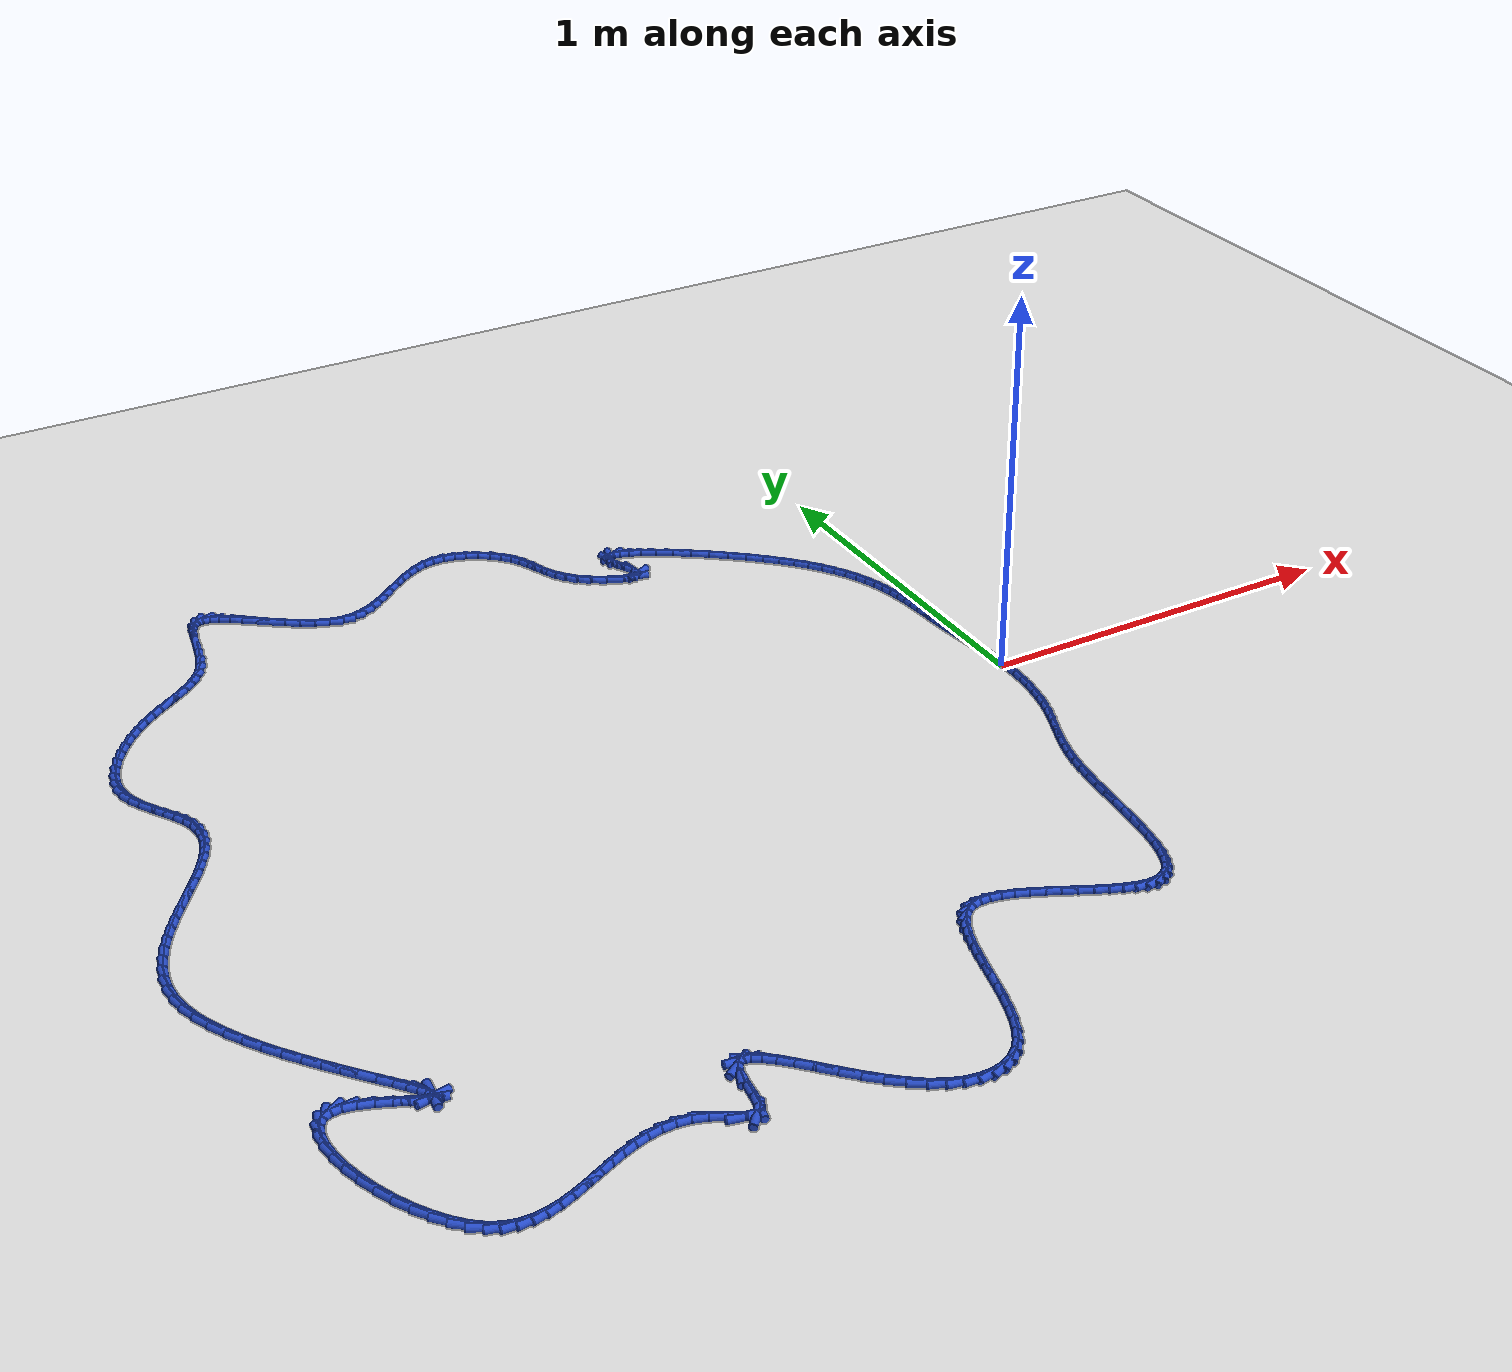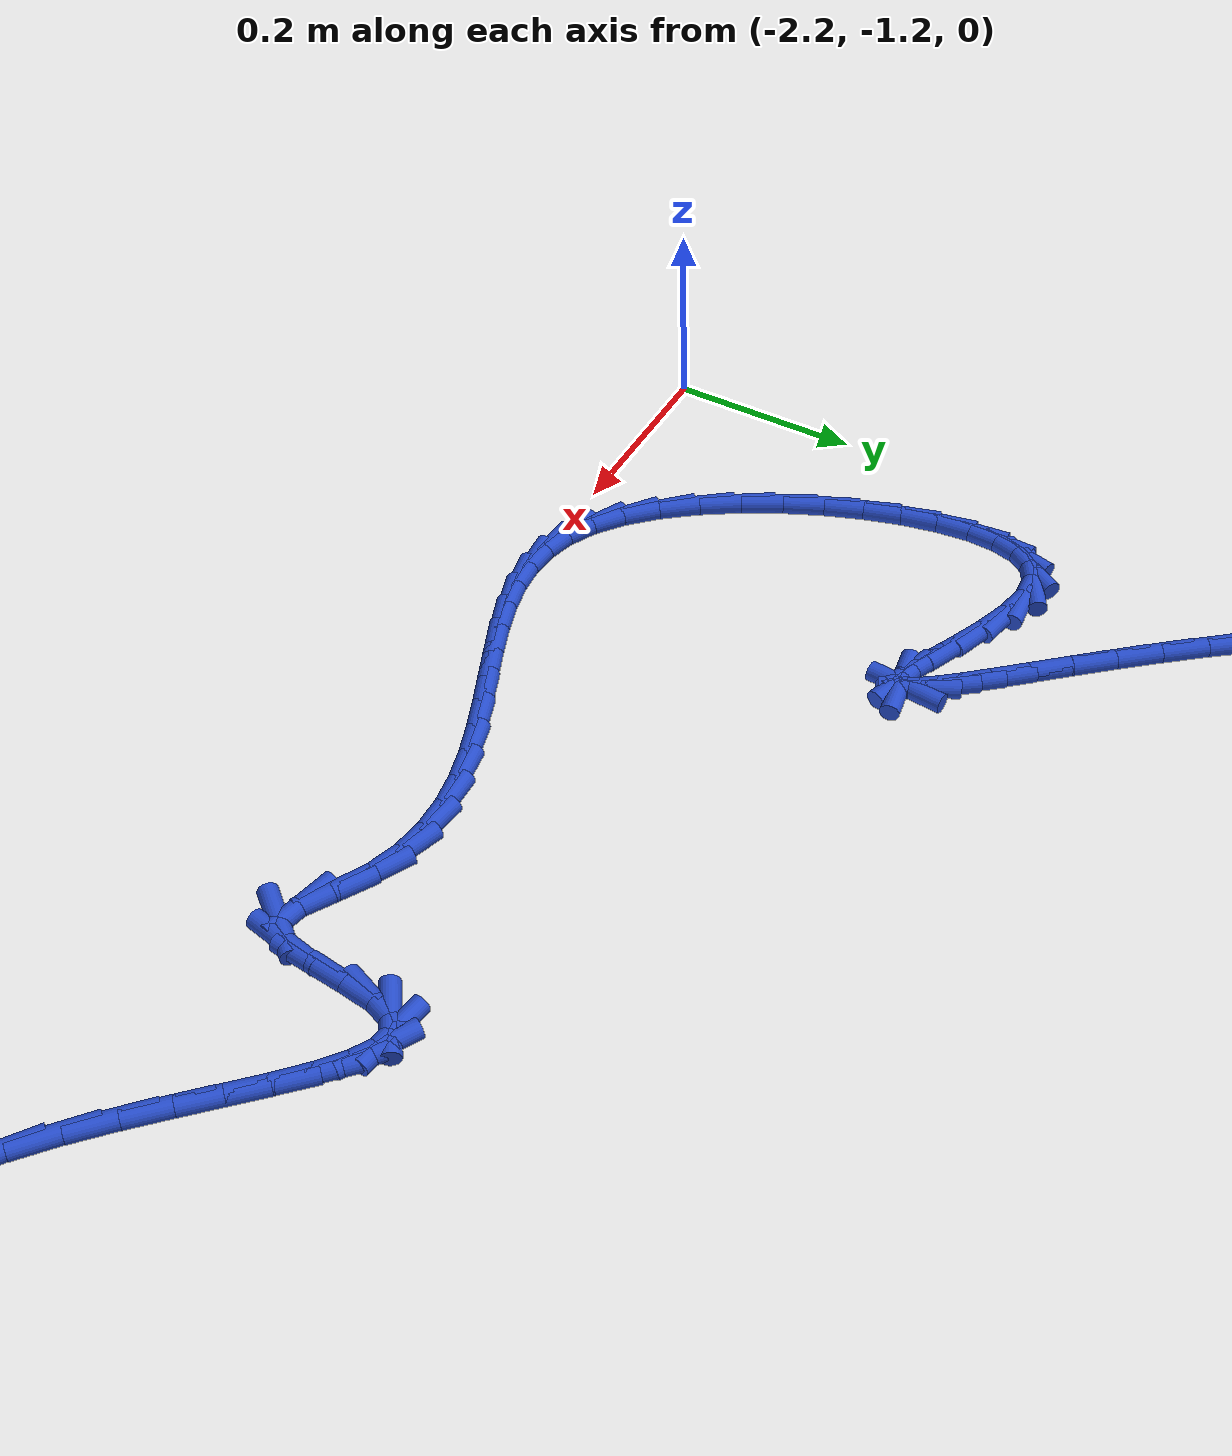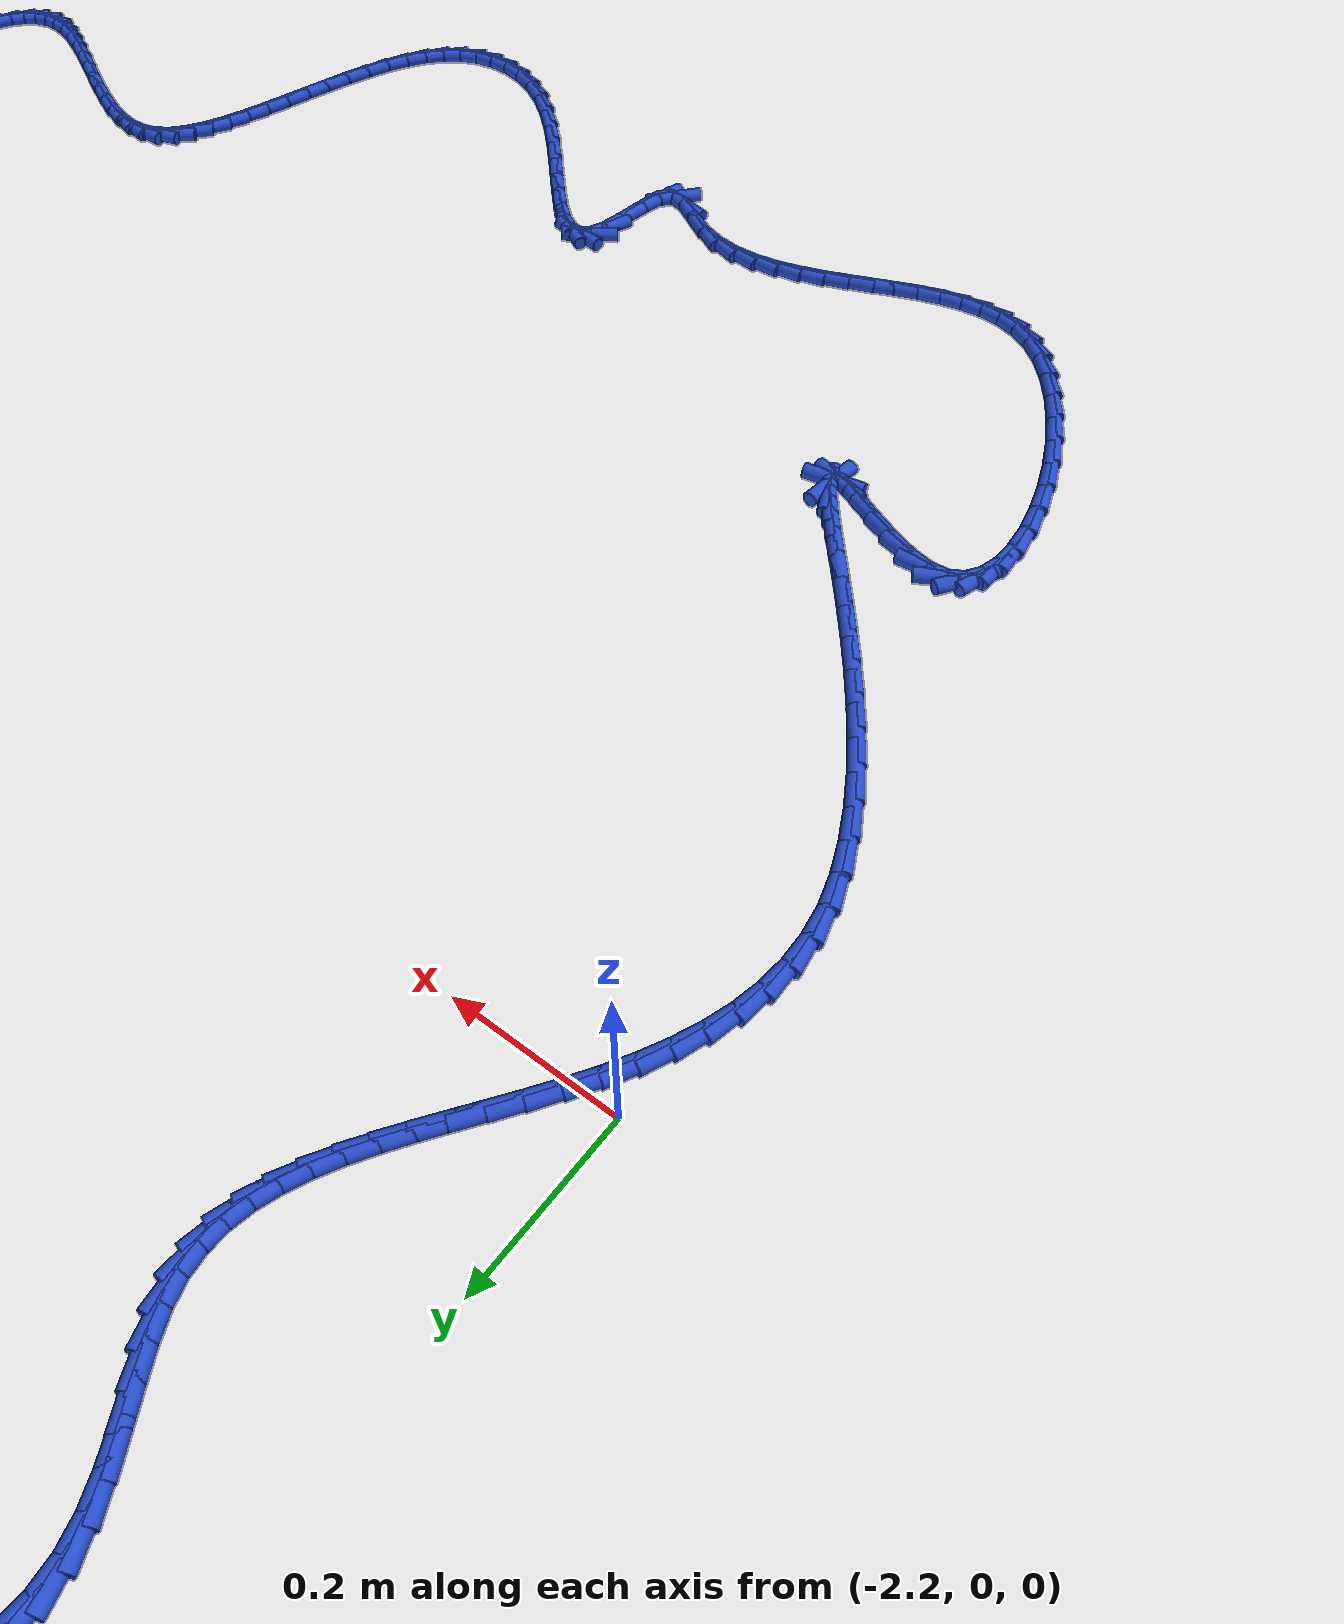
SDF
<sdf version="1.6">
 <world name="default">
  <light name="sun" type="directional">
   <pose>0 0 10 0 -0 0</pose>
   <diffuse>0.8 0.8 0.8 1</diffuse>
   <specular>0.2 0.2 0.2 1</specular>
   <attenuation>
    <range>1000</range>
    <constant>0.9</constant>
    <linear>0.01</linear>
    <quadratic>0.001</quadratic>
   </attenuation>
   <direction>-0.5 0.1 -0.9</direction>
  </light>
  <model name="ground_plane">
   <static>1</static>
   <link name="link">
    <collision name="collision">
     <geometry><plane><normal>0 0 1</normal><size>100 100</size></plane></geometry>
     <surface><friction><ode><mu>100</mu><mu2>50</mu2></ode></friction></surface>
    </collision>
    <visual name="visual">
     <cast_shadows>0</cast_shadows>
     <geometry><plane><normal>0 0 1</normal><size>100 100</size></plane></geometry>
     <material>
      <script><uri>file://media/materials/scripts/gazebo.material</uri><name>Gazebo/WhiteGlow</name></script>
     </material>
    </visual>
   </link>
  </model>
  <gravity>0 0 -9.8</gravity>
  <magnetic_field>6e-06 2.3e-05 -4.2e-05</magnetic_field>
  <atmosphere type="adiabatic"/>
  <physics name="default_physics" default="0" type="ode">
   <max_step_size>0.001</max_step_size>
   <real_time_factor>1</real_time_factor>
   <real_time_update_rate>1000</real_time_update_rate>
  </physics>
  <scene><ambient>0.4 0.4 0.4 1</ambient><background>0.7 0.7 0.7 1</background><shadows>1</shadows></scene>
  <spherical_coordinates>
   <surface_model>EARTH_WGS84</surface_model>
   <latitude_deg>0</latitude_deg>
   <longitude_deg>0</longitude_deg>
   <elevation>0</elevation>
   <heading_deg>0</heading_deg>
  </spherical_coordinates>
  <model name="line">
   <link name="link_0">
    <pose>6.938893903907228e-18 -5.551115123125783e-17 0.01 0 1.57 -1.5088992156621004</pose>
    <collision name="collision">
     <geometry><cylinder><radius>0.01</radius><length>0.08</length></cylinder></geometry>
    </collision>
    <visual name="visual">
     <material>
      <script><name>Gazebo/Blue</name><uri>file://media/materials/scripts/gazebo.material</uri></script>
     </material>
     <geometry><cylinder><radius>0.01</radius><length>0.08</length></cylinder></geometry>
    </visual>
   </link>
   <link name="link_1">
    <pose>-0.0019610523935351372 0.03164198278255451 0.01 0 1.57 -1.477729259361162</pose>
    <collision name="collision">
     <geometry><cylinder><radius>0.01</radius><length>0.08</length></cylinder></geometry>
    </collision>
    <visual name="visual">
     <material>
      <script><name>Gazebo/Blue</name><uri>file://media/materials/scripts/gazebo.material</uri></script>
     </material>
     <geometry><cylinder><radius>0.01</radius><length>0.08</length></cylinder></geometry>
    </visual>
   </link>
   <link name="link_2">
    <pose>-0.0048991539546748555 0.06312050651057965 0.01 0 1.57 -1.4550887492550557</pose>
    <collision name="collision">
     <geometry><cylinder><radius>0.01</radius><length>0.08</length></cylinder></geometry>
    </collision>
    <visual name="visual">
     <material>
      <script><name>Gazebo/Blue</name><uri>file://media/materials/scripts/gazebo.material</uri></script>
     </material>
     <geometry><cylinder><radius>0.01</radius><length>0.08</length></cylinder></geometry>
    </visual>
   </link>
   <link name="link_3">
    <pose>-0.008532511172250455 0.09438144936738568 0.01 0 1.57 -1.4409432503999768</pose>
    <collision name="collision">
     <geometry><cylinder><radius>0.01</radius><length>0.08</length></cylinder></geometry>
    </collision>
    <visual name="visual">
     <material>
      <script><name>Gazebo/Blue</name><uri>file://media/materials/scripts/gazebo.material</uri></script>
     </material>
     <geometry><cylinder><radius>0.01</radius><length>0.08</length></cylinder></geometry>
    </visual>
   </link>
   <link name="link_4">
    <pose>-0.012579330535093244 0.1253706895362829 0.01 0 1.57 -1.4353610421950345</pose>
    <collision name="collision">
     <geometry><cylinder><radius>0.01</radius><length>0.08</length></cylinder></geometry>
    </collision>
    <visual name="visual">
     <material>
      <script><name>Gazebo/Blue</name><uri>file://media/materials/scripts/gazebo.material</uri></script>
     </material>
     <geometry><cylinder><radius>0.01</radius><length>0.08</length></cylinder></geometry>
    </visual>
   </link>
   <link name="link_5">
    <pose>-0.016757818532034546 0.15603410520058167 0.01 0 1.57 -1.4385508494420716</pose>
    <collision name="collision">
     <geometry><cylinder><radius>0.01</radius><length>0.08</length></cylinder></geometry>
    </collision>
    <visual name="visual">
     <material>
      <script><name>Gazebo/Blue</name><uri>file://media/materials/scripts/gazebo.material</uri></script>
     </material>
     <geometry><cylinder><radius>0.01</radius><length>0.08</length></cylinder></geometry>
    </visual>
   </link>
   <link name="link_6">
    <pose>-0.020786181651905634 0.18631757454359216 0.01 0 1.57 -1.450888004517983</pose>
    <collision name="collision">
     <geometry><cylinder><radius>0.01</radius><length>0.08</length></cylinder></geometry>
    </collision>
    <visual name="visual">
     <material>
      <script><name>Gazebo/Blue</name><uri>file://media/materials/scripts/gazebo.material</uri></script>
     </material>
     <geometry><cylinder><radius>0.01</radius><length>0.08</length></cylinder></geometry>
    </visual>
   </link>
   <link name="link_7">
    <pose>-0.024382626383537838 0.21616697574862476 0.01 0 1.57 -1.4714316381948433</pose>
    <collision name="collision">
     <geometry><cylinder><radius>0.01</radius><length>0.08</length></cylinder></geometry>
    </collision>
    <visual name="visual">
     <material>
      <script><name>Gazebo/Blue</name><uri>file://media/materials/scripts/gazebo.material</uri></script>
     </material>
     <geometry><cylinder><radius>0.01</radius><length>0.08</length></cylinder></geometry>
    </visual>
   </link>
   <link name="link_8">
    <pose>-0.0273108293734939 0.24553917660356017 0.01 0 1.57 -1.488860914362205</pose>
    <collision name="collision">
     <geometry><cylinder><radius>0.01</radius><length>0.08</length></cylinder></geometry>
    </collision>
    <visual name="visual">
     <material>
      <script><name>Gazebo/Blue</name><uri>file://media/materials/scripts/gazebo.material</uri></script>
     </material>
     <geometry><cylinder><radius>0.01</radius><length>0.08</length></cylinder></geometry>
    </visual>
   </link>
   <link name="link_9">
    <pose>-0.02968712273781465 0.2744762775928978 0.01 0 1.57 -1.4972683014813488</pose>
    <collision name="collision">
     <geometry><cylinder><radius>0.01</radius><length>0.08</length></cylinder></geometry>
    </collision>
    <visual name="visual">
     <material>
      <script><name>Gazebo/Blue</name><uri>file://media/materials/scripts/gazebo.material</uri></script>
     </material>
     <geometry><cylinder><radius>0.01</radius><length>0.08</length></cylinder></geometry>
    </visual>
   </link>
   <link name="link_10">
    <pose>-0.031792638569010816 0.3030602094252879 0.01 0 1.57 -1.4961705828656344</pose>
    <collision name="collision">
     <geometry><cylinder><radius>0.01</radius><length>0.08</length></cylinder></geometry>
    </collision>
    <visual name="visual">
     <material>
      <script><name>Gazebo/Blue</name><uri>file://media/materials/scripts/gazebo.material</uri></script>
     </material>
     <geometry><cylinder><radius>0.01</radius><length>0.08</length></cylinder></geometry>
    </visual>
   </link>
   <link name="link_11">
    <pose>-0.033909442160713704 0.33137312835316146 0.01 0 1.57 -1.4853078793083827</pose>
    <collision name="collision">
     <geometry><cylinder><radius>0.01</radius><length>0.08</length></cylinder></geometry>
    </collision>
    <visual name="visual">
     <material>
      <script><name>Gazebo/Blue</name><uri>file://media/materials/scripts/gazebo.material</uri></script>
     </material>
     <geometry><cylinder><radius>0.01</radius><length>0.08</length></cylinder></geometry>
    </visual>
   </link>
   <link name="link_12">
    <pose>-0.036319598806554644 0.35949719062894975 0.01 0 1.57 -1.4646353467689244</pose>
    <collision name="collision">
     <geometry><cylinder><radius>0.01</radius><length>0.08</length></cylinder></geometry>
    </collision>
    <visual name="visual">
     <material>
      <script><name>Gazebo/Blue</name><uri>file://media/materials/scripts/gazebo.material</uri></script>
     </material>
     <geometry><cylinder><radius>0.01</radius><length>0.08</length></cylinder></geometry>
    </visual>
   </link>
   <link name="link_13">
    <pose>-0.03930517380016497 0.38751455250508404 0.01 0 1.57 -1.4343619140981554</pose>
    <collision name="collision">
     <geometry><cylinder><radius>0.01</radius><length>0.08</length></cylinder></geometry>
    </collision>
    <visual name="visual">
     <material>
      <script><name>Gazebo/Blue</name><uri>file://media/materials/scripts/gazebo.material</uri></script>
     </material>
     <geometry><cylinder><radius>0.01</radius><length>0.08</length></cylinder></geometry>
    </visual>
   </link>
   <link name="link_14">
    <pose>-0.04314823243517599 0.4155073702339952 0.01 0 1.57 -1.3949996194770606</pose>
    <collision name="collision">
     <geometry><cylinder><radius>0.01</radius><length>0.08</length></cylinder></geometry>
    </collision>
    <visual name="visual">
     <material>
      <script><name>Gazebo/Blue</name><uri>file://media/materials/scripts/gazebo.material</uri></script>
     </material>
     <geometry><cylinder><radius>0.01</radius><length>0.08</length></cylinder></geometry>
    </visual>
   </link>
   <link name="link_15">
    <pose>-0.04813084000521904 0.4435578000681148 0.01 0 1.57 -1.3474088254699563</pose>
    <collision name="collision">
     <geometry><cylinder><radius>0.01</radius><length>0.08</length></cylinder></geometry>
    </collision>
    <visual name="visual">
     <material>
      <script><name>Gazebo/Blue</name><uri>file://media/materials/scripts/gazebo.material</uri></script>
     </material>
     <geometry><cylinder><radius>0.01</radius><length>0.08</length></cylinder></geometry>
    </visual>
   </link>
   <link name="link_16">
    <pose>-0.05453506180392547 0.47174799825987396 0.01 0 1.57 -1.29281715194622</pose>
    <collision name="collision">
     <geometry><cylinder><radius>0.01</radius><length>0.08</length></cylinder></geometry>
    </collision>
    <visual name="visual">
     <material>
      <script><name>Gazebo/Blue</name><uri>file://media/materials/scripts/gazebo.material</uri></script>
     </material>
     <geometry><cylinder><radius>0.01</radius><length>0.08</length></cylinder></geometry>
    </visual>
   </link>
   <link name="link_17">
    <pose>-0.06264296312492657 0.5001601210617035 0.01 0 1.57 -1.2327889124168592</pose>
    <collision name="collision">
     <geometry><cylinder><radius>0.01</radius><length>0.08</length></cylinder></geometry>
    </collision>
    <visual name="visual">
     <material>
      <script><name>Gazebo/Blue</name><uri>file://media/materials/scripts/gazebo.material</uri></script>
     </material>
     <geometry><cylinder><radius>0.01</radius><length>0.08</length></cylinder></geometry>
    </visual>
   </link>
   <link name="link_18">
    <pose>-0.07273660926185364 0.528876324726035 0.01 0 1.57 -1.1691317881069503</pose>
    <collision name="collision">
     <geometry><cylinder><radius>0.01</radius><length>0.08</length></cylinder></geometry>
    </collision>
    <visual name="visual">
     <material>
      <script><name>Gazebo/Blue</name><uri>file://media/materials/scripts/gazebo.material</uri></script>
     </material>
     <geometry><cylinder><radius>0.01</radius><length>0.08</length></cylinder></geometry>
    </visual>
   </link>
   <link name="link_19">
    <pose>-0.0850980655083381 0.5579787655052993 0.01 0 1.57 -1.1037480698506</pose>
    <collision name="collision">
     <geometry><cylinder><radius>0.01</radius><length>0.08</length></cylinder></geometry>
    </collision>
    <visual name="visual">
     <material>
      <script><name>Gazebo/Blue</name><uri>file://media/materials/scripts/gazebo.material</uri></script>
     </material>
     <geometry><cylinder><radius>0.01</radius><length>0.08</length></cylinder></geometry>
    </visual>
   </link>
   <link name="link_20">
    <pose>-0.10000939715801119 0.587549599651928 0.01 0 1.57 -1.0384605199145034</pose>
    <collision name="collision">
     <geometry><cylinder><radius>0.01</radius><length>0.08</length></cylinder></geometry>
    </collision>
    <visual name="visual">
     <material>
      <script><name>Gazebo/Blue</name><uri>file://media/materials/scripts/gazebo.material</uri></script>
     </material>
     <geometry><cylinder><radius>0.01</radius><length>0.08</length></cylinder></geometry>
    </visual>
   </link>
   <link name="link_21">
    <pose>-0.11775266950450428 0.6176709834183519 0.01 0 1.57 -0.9748547876700769</pose>
    <collision name="collision">
     <geometry><cylinder><radius>0.01</radius><length>0.08</length></cylinder></geometry>
    </collision>
    <visual name="visual">
     <material>
      <script><name>Gazebo/Blue</name><uri>file://media/materials/scripts/gazebo.material</uri></script>
     </material>
     <geometry><cylinder><radius>0.01</radius><length>0.08</length></cylinder></geometry>
    </visual>
   </link>
   <link name="link_22">
    <pose>-0.13860994784144864 0.6484250730570021 0.01 0 1.57 -0.9141737521492417</pose>
    <collision name="collision">
     <geometry><cylinder><radius>0.01</radius><length>0.08</length></cylinder></geometry>
    </collision>
    <visual name="visual">
     <material>
      <script><name>Gazebo/Blue</name><uri>file://media/materials/scripts/gazebo.material</uri></script>
     </material>
     <geometry><cylinder><radius>0.01</radius><length>0.08</length></cylinder></geometry>
    </visual>
   </link>
   <link name="link_23">
    <pose>-0.1628632974624757 0.6798940248203104 0.01 0 1.57 -0.8572785468898613</pose>
    <collision name="collision">
     <geometry><cylinder><radius>0.01</radius><length>0.08</length></cylinder></geometry>
    </collision>
    <visual name="visual">
     <material>
      <script><name>Gazebo/Blue</name><uri>file://media/materials/scripts/gazebo.material</uri></script>
     </material>
     <geometry><cylinder><radius>0.01</radius><length>0.08</length></cylinder></geometry>
    </visual>
   </link>
   <link name="link_24">
    <pose>-0.1907947836612167 0.7121599949607074 0.01 0 1.57 -0.8049406382359237</pose>
    <collision name="collision">
     <geometry><cylinder><radius>0.01</radius><length>0.08</length></cylinder></geometry>
    </collision>
    <visual name="visual">
     <material>
      <script><name>Gazebo/Blue</name><uri>file://media/materials/scripts/gazebo.material</uri></script>
     </material>
     <geometry><cylinder><radius>0.01</radius><length>0.08</length></cylinder></geometry>
    </visual>
   </link>
   <link name="link_25">
    <pose>-0.2226429407834202 0.7452779115926293 0.01 0 1.57 -0.7602624368892206</pose>
    <collision name="collision">
     <geometry><cylinder><radius>0.01</radius><length>0.08</length></cylinder></geometry>
    </collision>
    <visual name="visual">
     <material>
      <script><name>Gazebo/Blue</name><uri>file://media/materials/scripts/gazebo.material</uri></script>
     </material>
     <geometry><cylinder><radius>0.01</radius><length>0.08</length></cylinder></geometry>
    </visual>
   </link>
   <link name="link_26">
    <pose>-0.2579929372510982 0.7788940294981375 0.01 0 1.57 -0.7226090901260351</pose>
    <collision name="collision">
     <geometry><cylinder><radius>0.01</radius><length>0.08</length></cylinder></geometry>
    </collision>
    <visual name="visual">
     <material>
      <script><name>Gazebo/Blue</name><uri>file://media/materials/scripts/gazebo.material</uri></script>
     </material>
     <geometry><cylinder><radius>0.01</radius><length>0.08</length></cylinder></geometry>
    </visual>
   </link>
   <link name="link_27">
    <pose>-0.2959259470729695 0.8123393603942715 0.01 0 1.57 -0.6889044936429538</pose>
    <collision name="collision">
     <geometry><cylinder><radius>0.01</radius><length>0.08</length></cylinder></geometry>
    </collision>
    <visual name="visual">
     <material>
      <script><name>Gazebo/Blue</name><uri>file://media/materials/scripts/gazebo.material</uri></script>
     </material>
     <geometry><cylinder><radius>0.01</radius><length>0.08</length></cylinder></geometry>
    </visual>
   </link>
   <link name="link_28">
    <pose>-0.3355101200194297 0.8449367694775937 0.01 0 1.57 -0.6567807551668474</pose>
    <collision name="collision">
     <geometry><cylinder><radius>0.01</radius><length>0.08</length></cylinder></geometry>
    </collision>
    <visual name="visual">
     <material>
      <script><name>Gazebo/Blue</name><uri>file://media/materials/scripts/gazebo.material</uri></script>
     </material>
     <geometry><cylinder><radius>0.01</radius><length>0.08</length></cylinder></geometry>
    </visual>
   </link>
   <link name="link_29">
    <pose>-0.37581360586087376 0.876009121944666 0.01 0 1.57 -0.62409989787336</pose>
    <collision name="collision">
     <geometry><cylinder><radius>0.01</radius><length>0.08</length></cylinder></geometry>
    </collision>
    <visual name="visual">
     <material>
      <script><name>Gazebo/Blue</name><uri>file://media/materials/scripts/gazebo.material</uri></script>
     </material>
     <geometry><cylinder><radius>0.01</radius><length>0.08</length></cylinder></geometry>
    </visual>
   </link>
   <link name="link_30">
    <pose>-0.4159045543676966 0.9048792829920496 0.01 0 1.57 -0.5884728200253018</pose>
    <collision name="collision">
     <geometry><cylinder><radius>0.01</radius><length>0.08</length></cylinder></geometry>
    </collision>
    <visual name="visual">
     <material>
      <script><name>Gazebo/Blue</name><uri>file://media/materials/scripts/gazebo.material</uri></script>
     </material>
     <geometry><cylinder><radius>0.01</radius><length>0.08</length></cylinder></geometry>
    </visual>
   </link>
   <link name="link_31">
    <pose>-0.45485111531029343 0.9308701178163069 0.01 0 1.57 -0.5466219645819852</pose>
    <collision name="collision">
     <geometry><cylinder><radius>0.01</radius><length>0.08</length></cylinder></geometry>
    </collision>
    <visual name="visual">
     <material>
      <script><name>Gazebo/Blue</name><uri>file://media/materials/scripts/gazebo.material</uri></script>
     </material>
     <geometry><cylinder><radius>0.01</radius><length>0.08</length></cylinder></geometry>
    </visual>
   </link>
   <link name="link_32">
    <pose>-0.4917214384590594 0.9533044916139998 0.01 0 1.57 -0.49319168367402105</pose>
    <collision name="collision">
     <geometry><cylinder><radius>0.01</radius><length>0.08</length></cylinder></geometry>
    </collision>
    <visual name="visual">
     <material>
      <script><name>Gazebo/Blue</name><uri>file://media/materials/scripts/gazebo.material</uri></script>
     </material>
     <geometry><cylinder><radius>0.01</radius><length>0.08</length></cylinder></geometry>
    </visual>
   </link>
   <link name="link_33">
    <pose>-0.5255836735843894 0.9715052695816899 0.01 0 1.57 -0.41798007829533684</pose>
    <collision name="collision">
     <geometry><cylinder><radius>0.01</radius><length>0.08</length></cylinder></geometry>
    </collision>
    <visual name="visual">
     <material>
      <script><name>Gazebo/Blue</name><uri>file://media/materials/scripts/gazebo.material</uri></script>
     </material>
     <geometry><cylinder><radius>0.01</radius><length>0.08</length></cylinder></geometry>
    </visual>
   </link>
   <link name="link_34">
    <pose>-0.5555059704566787 0.9847953169159389 0.01 0 1.57 -0.29829226663411934</pose>
    <collision name="collision">
     <geometry><cylinder><radius>0.01</radius><length>0.08</length></cylinder></geometry>
    </collision>
    <visual name="visual">
     <material>
      <script><name>Gazebo/Blue</name><uri>file://media/materials/scripts/gazebo.material</uri></script>
     </material>
     <geometry><cylinder><radius>0.01</radius><length>0.08</length></cylinder></geometry>
    </visual>
   </link>
   <link name="link_35">
    <pose>-0.5805564788463223 0.9924974988133093 0.01 0 1.57 -0.0745326102867308</pose>
    <collision name="collision">
     <geometry><cylinder><radius>0.01</radius><length>0.08</length></cylinder></geometry>
    </collision>
    <visual name="visual">
     <material>
      <script><name>Gazebo/Blue</name><uri>file://media/materials/scripts/gazebo.material</uri></script>
     </material>
     <geometry><cylinder><radius>0.01</radius><length>0.08</length></cylinder></geometry>
    </visual>
   </link>
   <link name="link_36">
    <pose>-0.5998033485237151 0.9939346804703619 0.01 0 1.57 0.4145032493987455</pose>
    <collision name="collision">
     <geometry><cylinder><radius>0.01</radius><length>0.08</length></cylinder></geometry>
    </collision>
    <visual name="visual">
     <material>
      <script><name>Gazebo/Blue</name><uri>file://media/materials/scripts/gazebo.material</uri></script>
     </material>
     <geometry><cylinder><radius>0.01</radius><length>0.08</length></cylinder></geometry>
    </visual>
   </link>
   <link name="link_37">
    <pose>-0.6123147292592526 0.9884297270836595 0.01 0 1.57 1.217215590794292</pose>
    <collision name="collision">
     <geometry><cylinder><radius>0.01</radius><length>0.08</length></cylinder></geometry>
    </collision>
    <visual name="visual">
     <material>
      <script><name>Gazebo/Blue</name><uri>file://media/materials/scripts/gazebo.material</uri></script>
     </material>
     <geometry><cylinder><radius>0.01</radius><length>0.08</length></cylinder></geometry>
    </visual>
   </link>
   <link name="link_38">
    <pose>-0.6171587708233295 0.9753055038497636 0.01 0 1.57 -1.397254527426382</pose>
    <collision name="collision">
     <geometry><cylinder><radius>0.01</radius><length>0.08</length></cylinder></geometry>
    </collision>
    <visual name="visual">
     <material>
      <script><name>Gazebo/Blue</name><uri>file://media/materials/scripts/gazebo.material</uri></script>
     </material>
     <geometry><cylinder><radius>0.01</radius><length>0.08</length></cylinder></geometry>
    </visual>
   </link>
   <link name="link_39">
    <pose>-0.6134036229863409 0.9538848759652357 0.01 0 1.57 -1.1716803246438623</pose>
    <collision name="collision">
     <geometry><cylinder><radius>0.01</radius><length>0.08</length></cylinder></geometry>
    </collision>
    <visual name="visual">
     <material>
      <script><name>Gazebo/Blue</name><uri>file://media/materials/scripts/gazebo.material</uri></script>
     </material>
     <geometry><cylinder><radius>0.01</radius><length>0.08</length></cylinder></geometry>
    </visual>
   </link>
   <link name="link_40">
    <pose>-0.6008384807656233 0.9240921200666977 0.01 0 1.57 -1.1612288086682636</pose>
    <collision name="collision">
     <geometry><cylinder><radius>0.01</radius><length>0.08</length></cylinder></geometry>
    </collision>
    <visual name="visual">
     <material>
      <script><name>Gazebo/Blue</name><uri>file://media/materials/scripts/gazebo.material</uri></script>
     </material>
     <geometry><cylinder><radius>0.01</radius><length>0.08</length></cylinder></geometry>
    </visual>
   </link>
   <link name="link_41">
    <pose>-0.5870671780746236 0.8923695686991802 0.01 0 1.57 -1.4590879658373426</pose>
    <collision name="collision">
     <geometry><cylinder><radius>0.01</radius><length>0.08</length></cylinder></geometry>
    </collision>
    <visual name="visual">
     <material>
      <script><name>Gazebo/Blue</name><uri>file://media/materials/scripts/gazebo.material</uri></script>
     </material>
     <geometry><cylinder><radius>0.01</radius><length>0.08</length></cylinder></geometry>
    </visual>
   </link>
   <link name="link_42">
    <pose>-0.584461156380133 0.8691378904946149 0.01 0 1.57 0.4635677971690647</pose>
    <collision name="collision">
     <geometry><cylinder><radius>0.01</radius><length>0.08</length></cylinder></geometry>
    </collision>
    <visual name="visual">
     <material>
      <script><name>Gazebo/Blue</name><uri>file://media/materials/scripts/gazebo.material</uri></script>
     </material>
     <geometry><cylinder><radius>0.01</radius><length>0.08</length></cylinder></geometry>
    </visual>
   </link>
   <link name="link_43">
    <pose>-0.6003962649047978 0.8611719259315979 0.01 0 1.57 -0.17376023900306845</pose>
    <collision name="collision">
     <geometry><cylinder><radius>0.01</radius><length>0.08</length></cylinder></geometry>
    </collision>
    <visual name="visual">
     <material>
      <script><name>Gazebo/Blue</name><uri>file://media/materials/scripts/gazebo.material</uri></script>
     </material>
     <geometry><cylinder><radius>0.01</radius><length>0.08</length></cylinder></geometry>
    </visual>
   </link>
   <link name="link_44">
    <pose>-0.6301405659923899 0.8663929543788353 0.01 0 1.57 -0.3854750708869507</pose>
    <collision name="collision">
     <geometry><cylinder><radius>0.01</radius><length>0.08</length></cylinder></geometry>
    </collision>
    <visual name="visual">
     <material>
      <script><name>Gazebo/Blue</name><uri>file://media/materials/scripts/gazebo.material</uri></script>
     </material>
     <geometry><cylinder><radius>0.01</radius><length>0.08</length></cylinder></geometry>
    </visual>
   </link>
   <link name="link_45">
    <pose>-0.6671908218942201 0.8814270297629732 0.01 0 1.57 -0.516011976652437</pose>
    <collision name="collision">
     <geometry><cylinder><radius>0.01</radius><length>0.08</length></cylinder></geometry>
    </collision>
    <visual name="visual">
     <material>
      <script><name>Gazebo/Blue</name><uri>file://media/materials/scripts/gazebo.material</uri></script>
     </material>
     <geometry><cylinder><radius>0.01</radius><length>0.08</length></cylinder></geometry>
    </visual>
   </link>
   <link name="link_46">
    <pose>-0.705043794861601 0.9029002060106583 0.01 0 1.57 -0.6504916208534457</pose>
    <collision name="collision">
     <geometry><cylinder><radius>0.01</radius><length>0.08</length></cylinder></geometry>
    </collision>
    <visual name="visual">
     <material>
      <script><name>Gazebo/Blue</name><uri>file://media/materials/scripts/gazebo.material</uri></script>
     </material>
     <geometry><cylinder><radius>0.01</radius><length>0.08</length></cylinder></geometry>
    </visual>
   </link>
   <link name="link_47">
    <pose>-0.7373732192416151 0.9275022650520145 0.01 0 1.57 -0.8126155202004183</pose>
    <collision name="collision">
     <geometry><cylinder><radius>0.01</radius><length>0.08</length></cylinder></geometry>
    </collision>
    <visual name="visual">
     <material>
      <script><name>Gazebo/Blue</name><uri>file://media/materials/scripts/gazebo.material</uri></script>
     </material>
     <geometry><cylinder><radius>0.01</radius><length>0.08</length></cylinder></geometry>
    </visual>
   </link>
   <link name="link_48">
    <pose>-0.7618691402108032 0.9533692703305908 0.01 0 1.57 -0.9690107859283018</pose>
    <collision name="collision">
     <geometry><cylinder><radius>0.01</radius><length>0.08</length></cylinder></geometry>
    </collision>
    <visual name="visual">
     <material>
      <script><name>Gazebo/Blue</name><uri>file://media/materials/scripts/gazebo.material</uri></script>
     </material>
     <geometry><cylinder><radius>0.01</radius><length>0.08</length></cylinder></geometry>
    </visual>
   </link>
   <link name="link_49">
    <pose>-0.7802081149660071 0.9800728361929484 0.01 0 1.57 -1.0941935787418033</pose>
    <collision name="collision">
     <geometry><cylinder><radius>0.01</radius><length>0.08</length></cylinder></geometry>
    </collision>
    <visual name="visual">
     <material>
      <script><name>Gazebo/Blue</name><uri>file://media/materials/scripts/gazebo.material</uri></script>
     </material>
     <geometry><cylinder><radius>0.01</radius><length>0.08</length></cylinder></geometry>
    </visual>
   </link>
   <link name="link_50">
    <pose>-0.7942377129343955 1.007246158829731 0.01 0 1.57 -1.169690654146283</pose>
    <collision name="collision">
     <geometry><cylinder><radius>0.01</radius><length>0.08</length></cylinder></geometry>
    </collision>
    <visual name="visual">
     <material>
      <script><name>Gazebo/Blue</name><uri>file://media/materials/scripts/gazebo.material</uri></script>
     </material>
     <geometry><cylinder><radius>0.01</radius><length>0.08</length></cylinder></geometry>
    </visual>
   </link>
   <link name="link_51">
    <pose>-0.8058055035431388 1.034522434431586 0.01 0 1.57 -1.1855571219605192</pose>
    <collision name="collision">
     <geometry><cylinder><radius>0.01</radius><length>0.08</length></cylinder></geometry>
    </collision>
    <visual name="visual">
     <material>
      <script><name>Gazebo/Blue</name><uri>file://media/materials/scripts/gazebo.material</uri></script>
     </material>
     <geometry><cylinder><radius>0.01</radius><length>0.08</length></cylinder></geometry>
    </visual>
   </link>
   <link name="link_52">
    <pose>-0.8167590562194057 1.061534859189157 0.01 0 1.57 -1.138054788118516</pose>
    <collision name="collision">
     <geometry><cylinder><radius>0.01</radius><length>0.08</length></cylinder></geometry>
    </collision>
    <visual name="visual">
     <material>
      <script><name>Gazebo/Blue</name><uri>file://media/materials/scripts/gazebo.material</uri></script>
     </material>
     <geometry><cylinder><radius>0.01</radius><length>0.08</length></cylinder></geometry>
    </visual>
   </link>
   <link name="link_53">
    <pose>-0.8289459403903655 1.0879166292930893 0.01 0 1.57 -1.0293000248883601</pose>
    <collision name="collision">
     <geometry><cylinder><radius>0.01</radius><length>0.08</length></cylinder></geometry>
    </collision>
    <visual name="visual">
     <material>
      <script><name>Gazebo/Blue</name><uri>file://media/materials/scripts/gazebo.material</uri></script>
     </material>
     <geometry><cylinder><radius>0.01</radius><length>0.08</length></cylinder></geometry>
    </visual>
   </link>
   <link name="link_54">
    <pose>-0.8442137254831876 1.1133009409340282 0.01 0 1.57 -0.8795882266533045</pose>
    <collision name="collision">
     <geometry><cylinder><radius>0.01</radius><length>0.08</length></cylinder></geometry>
    </collision>
    <visual name="visual">
     <material>
      <script><name>Gazebo/Blue</name><uri>file://media/materials/scripts/gazebo.material</uri></script>
     </material>
     <geometry><cylinder><radius>0.01</radius><length>0.08</length></cylinder></geometry>
    </visual>
   </link>
   <link name="link_55">
    <pose>-0.8640414653441205 1.1372657448645194 0.01 0 1.57 -0.7380993372572499</pose>
    <collision name="collision">
     <geometry><cylinder><radius>0.01</radius><length>0.08</length></cylinder></geometry>
    </collision>
    <visual name="visual">
     <material>
      <script><name>Gazebo/Blue</name><uri>file://media/materials/scripts/gazebo.material</uri></script>
     </material>
     <geometry><cylinder><radius>0.01</radius><length>0.08</length></cylinder></geometry>
    </visual>
   </link>
   <link name="link_56">
    <pose>-0.888058248411459 1.1591116571605773 0.01 0 1.57 -0.6073159047985717</pose>
    <collision name="collision">
     <geometry><cylinder><radius>0.01</radius><length>0.08</length></cylinder></geometry>
    </collision>
    <visual name="visual">
     <material>
      <script><name>Gazebo/Blue</name><uri>file://media/materials/scripts/gazebo.material</uri></script>
     </material>
     <geometry><cylinder><radius>0.01</radius><length>0.08</length></cylinder></geometry>
    </visual>
   </link>
   <link name="link_57">
    <pose>-0.9153138957969427 1.178052453941131 0.01 0 1.57 -0.4764899474320557</pose>
    <collision name="collision">
     <geometry><cylinder><radius>0.01</radius><length>0.08</length></cylinder></geometry>
    </collision>
    <visual name="visual">
     <material>
      <script><name>Gazebo/Blue</name><uri>file://media/materials/scripts/gazebo.material</uri></script>
     </material>
     <geometry><cylinder><radius>0.01</radius><length>0.08</length></cylinder></geometry>
    </visual>
   </link>
   <link name="link_58">
    <pose>-0.944858028184237 1.1933018812782483 0.01 0 1.57 -0.33560766737780984</pose>
    <collision name="collision">
     <geometry><cylinder><radius>0.01</radius><length>0.08</length></cylinder></geometry>
    </collision>
    <visual name="visual">
     <material>
      <script><name>Gazebo/Blue</name><uri>file://media/materials/scripts/gazebo.material</uri></script>
     </material>
     <geometry><cylinder><radius>0.01</radius><length>0.08</length></cylinder></geometry>
    </visual>
   </link>
   <link name="link_59">
    <pose>-0.975740266257008 1.2040736852439968 0.01 0 1.57 -0.17435266647738792</pose>
    <collision name="collision">
     <geometry><cylinder><radius>0.01</radius><length>0.08</length></cylinder></geometry>
    </collision>
    <visual name="visual">
     <material>
      <script><name>Gazebo/Blue</name><uri>file://media/materials/scripts/gazebo.material</uri></script>
     </material>
     <geometry><cylinder><radius>0.01</radius><length>0.08</length></cylinder></geometry>
    </visual>
   </link>
   <link name="link_60">
    <pose>-1.0070102306989215 1.2095816119104448 0.01 0 1.57 0.017577485361048552</pose>
    <collision name="collision">
     <geometry><cylinder><radius>0.01</radius><length>0.08</length></cylinder></geometry>
    </collision>
    <visual name="visual">
     <material>
      <script><name>Gazebo/Blue</name><uri>file://media/materials/scripts/gazebo.material</uri></script>
     </material>
     <geometry><cylinder><radius>0.01</radius><length>0.08</length></cylinder></geometry>
    </visual>
   </link>
   <link name="link_61">
    <pose>-1.0377189499454738 1.2090417742487674 0.01 0 1.57 0.22717992599412895</pose>
    <collision name="collision">
     <geometry><cylinder><radius>0.01</radius><length>0.08</length></cylinder></geometry>
    </collision>
    <visual name="visual">
     <material>
      <script><name>Gazebo/Blue</name><uri>file://media/materials/scripts/gazebo.material</uri></script>
     </material>
     <geometry><cylinder><radius>0.01</radius><length>0.08</length></cylinder></geometry>
    </visual>
   </link>
   <link name="link_62">
    <pose>-1.0672424989679263 1.2022167965816626 0.01 0 1.57 0.4022519639422933</pose>
    <collision name="collision">
     <geometry><cylinder><radius>0.01</radius><length>0.08</length></cylinder></geometry>
    </collision>
    <visual name="visual">
     <material>
      <script><name>Gazebo/Blue</name><uri>file://media/materials/scripts/gazebo.material</uri></script>
     </material>
     <geometry><cylinder><radius>0.01</radius><length>0.08</length></cylinder></geometry>
    </visual>
   </link>
   <link name="link_63">
    <pose>-1.0956956959883863 1.1901113763752855 0.01 0 1.57 0.5310340651734727</pose>
    <collision name="collision">
     <geometry><cylinder><radius>0.01</radius><length>0.08</length></cylinder></geometry>
    </collision>
    <visual name="visual">
     <material>
      <script><name>Gazebo/Blue</name><uri>file://media/materials/scripts/gazebo.material</uri></script>
     </material>
     <geometry><cylinder><radius>0.01</radius><length>0.08</length></cylinder></geometry>
    </visual>
   </link>
   <link name="link_64">
    <pose>-1.123295445762803 1.1739018525176905 0.01 0 1.57 0.6172434148043432</pose>
    <collision name="collision">
     <geometry><cylinder><radius>0.01</radius><length>0.08</length></cylinder></geometry>
    </collision>
    <visual name="visual">
     <material>
      <script><name>Gazebo/Blue</name><uri>file://media/materials/scripts/gazebo.material</uri></script>
     </material>
     <geometry><cylinder><radius>0.01</radius><length>0.08</length></cylinder></geometry>
    </visual>
   </link>
   <link name="link_65">
    <pose>-1.1502586530471257 1.1547645638969322 0.01 0 1.57 0.6667386898226974</pose>
    <collision name="collision">
     <geometry><cylinder><radius>0.01</radius><length>0.08</length></cylinder></geometry>
    </collision>
    <visual name="visual">
     <material>
      <script><name>Gazebo/Blue</name><uri>file://media/materials/scripts/gazebo.material</uri></script>
     </material>
     <geometry><cylinder><radius>0.01</radius><length>0.08</length></cylinder></geometry>
    </visual>
   </link>
   <link name="link_66">
    <pose>-1.1768022225973038 1.1338758494010648 0.01 0 1.57 0.6837297910393486</pose>
    <collision name="collision">
     <geometry><cylinder><radius>0.01</radius><length>0.08</length></cylinder></geometry>
    </collision>
    <visual name="visual">
     <material>
      <script><name>Gazebo/Blue</name><uri>file://media/materials/scripts/gazebo.material</uri></script>
     </material>
     <geometry><cylinder><radius>0.01</radius><length>0.08</length></cylinder></geometry>
    </visual>
   </link>
   <link name="link_67">
    <pose>-1.2031430591692867 1.112412047918144 0.01 0 1.57 0.6695962123599518</pose>
    <collision name="collision">
     <geometry><cylinder><radius>0.01</radius><length>0.08</length></cylinder></geometry>
    </collision>
    <visual name="visual">
     <material>
      <script><name>Gazebo/Blue</name><uri>file://media/materials/scripts/gazebo.material</uri></script>
     </material>
     <geometry><cylinder><radius>0.01</radius><length>0.08</length></cylinder></geometry>
    </visual>
   </link>
   <link name="link_68">
    <pose>-1.2294980675190232 1.0915494983362228 0.01 0 1.57 0.6226090642263317</pose>
    <collision name="collision">
     <geometry><cylinder><radius>0.01</radius><length>0.08</length></cylinder></geometry>
    </collision>
    <visual name="visual">
     <material>
      <script><name>Gazebo/Blue</name><uri>file://media/materials/scripts/gazebo.material</uri></script>
     </material>
     <geometry><cylinder><radius>0.01</radius><length>0.08</length></cylinder></geometry>
    </visual>
   </link>
   <link name="link_69">
    <pose>-1.2560841524024635 1.0724645395433572 0.01 0 1.57 0.5379840909663278</pose>
    <collision name="collision">
     <geometry><cylinder><radius>0.01</radius><length>0.08</length></cylinder></geometry>
    </collision>
    <visual name="visual">
     <material>
      <script><name>Gazebo/Blue</name><uri>file://media/materials/scripts/gazebo.material</uri></script>
     </material>
     <geometry><cylinder><radius>0.01</radius><length>0.08</length></cylinder></geometry>
    </visual>
   </link>
   <link name="link_70">
    <pose>-1.2831182185755559 1.0563335104276004 0.01 0 1.57 0.4088434280261329</pose>
    <collision name="collision">
     <geometry><cylinder><radius>0.01</radius><length>0.08</length></cylinder></geometry>
    </collision>
    <visual name="visual">
     <material>
      <script><name>Gazebo/Blue</name><uri>file://media/materials/scripts/gazebo.material</uri></script>
     </material>
     <geometry><cylinder><radius>0.01</radius><length>0.08</length></cylinder></geometry>
    </visual>
   </link>
   <link name="link_71">
    <pose>-1.3108171707942502 1.044332749877008 0.01 0 1.57 0.2300717068614746</pose>
    <collision name="collision">
     <geometry><cylinder><radius>0.01</radius><length>0.08</length></cylinder></geometry>
    </collision>
    <visual name="visual">
     <material>
      <script><name>Gazebo/Blue</name><uri>file://media/materials/scripts/gazebo.material</uri></script>
     </material>
     <geometry><cylinder><radius>0.01</radius><length>0.08</length></cylinder></geometry>
    </visual>
   </link>
   <link name="link_72">
    <pose>-1.3393979138144954 1.0376385967796342 0.01 0 1.57 0.007116145084728164</pose>
    <collision name="collision">
     <geometry><cylinder><radius>0.01</radius><length>0.08</length></cylinder></geometry>
    </collision>
    <visual name="visual">
     <material>
      <script><name>Gazebo/Blue</name><uri>file://media/materials/scripts/gazebo.material</uri></script>
     </material>
     <geometry><cylinder><radius>0.01</radius><length>0.08</length></cylinder></geometry>
    </visual>
   </link>
   <link name="link_73">
    <pose>-1.3690773523922417 1.0374273900235333 0.01 0 1.57 -0.22430684001839685</pose>
    <collision name="collision">
     <geometry><cylinder><radius>0.01</radius><length>0.08</length></cylinder></geometry>
    </collision>
    <visual name="visual">
     <material>
      <script><name>Gazebo/Blue</name><uri>file://media/materials/scripts/gazebo.material</uri></script>
     </material>
     <geometry><cylinder><radius>0.01</radius><length>0.08</length></cylinder></geometry>
    </visual>
   </link>
   <link name="link_74">
    <pose>-1.3999722618208565 1.0444759405049506 0.01 0 1.57 -0.3965158766833829</pose>
    <collision name="collision">
     <geometry><cylinder><radius>0.01</radius><length>0.08</length></cylinder></geometry>
    </collision>
    <visual name="visual">
     <material>
      <script><name>Gazebo/Blue</name><uri>file://media/materials/scripts/gazebo.material</uri></script>
     </material>
     <geometry><cylinder><radius>0.01</radius><length>0.08</length></cylinder></geometry>
    </visual>
   </link>
   <link name="link_75">
    <pose>-1.431753696842944 1.0577825832153878 0.01 0 1.57 -0.5111488755094384</pose>
    <collision name="collision">
     <geometry><cylinder><radius>0.01</radius><length>0.08</length></cylinder></geometry>
    </collision>
    <visual name="visual">
     <material>
      <script><name>Gazebo/Blue</name><uri>file://media/materials/scripts/gazebo.material</uri></script>
     </material>
     <geometry><cylinder><radius>0.01</radius><length>0.08</length></cylinder></geometry>
    </visual>
   </link>
   <link name="link_76">
    <pose>-1.4639687344368904 1.0758509677072075 0.01 0 1.57 -0.5852008580035079</pose>
    <collision name="collision">
     <geometry><cylinder><radius>0.01</radius><length>0.08</length></cylinder></geometry>
    </collision>
    <visual name="visual">
     <material>
      <script><name>Gazebo/Blue</name><uri>file://media/materials/scripts/gazebo.material</uri></script>
     </material>
     <geometry><cylinder><radius>0.01</radius><length>0.08</length></cylinder></geometry>
    </visual>
   </link>
   <link name="link_77">
    <pose>-1.4961644465363328 1.0971847234036554 0.01 0 1.57 -0.6294382197048156</pose>
    <collision name="collision">
     <geometry><cylinder><radius>0.01</radius><length>0.08</length></cylinder></geometry>
    </collision>
    <visual name="visual">
     <material>
      <script><name>Gazebo/Blue</name><uri>file://media/materials/scripts/gazebo.material</uri></script>
     </material>
     <geometry><cylinder><radius>0.01</radius><length>0.08</length></cylinder></geometry>
    </visual>
   </link>
   <link name="link_78">
    <pose>-1.5278879050749108 1.12028747972798 0.01 0 1.57 -0.6492258495094699</pose>
    <collision name="collision">
     <geometry><cylinder><radius>0.01</radius><length>0.08</length></cylinder></geometry>
    </collision>
    <visual name="visual">
     <material>
      <script><name>Gazebo/Blue</name><uri>file://media/materials/scripts/gazebo.material</uri></script>
     </material>
     <geometry><cylinder><radius>0.01</radius><length>0.08</length></cylinder></geometry>
    </visual>
   </link>
   <link name="link_79">
    <pose>-1.5586861819862612 1.1436628661034258 0.01 0 1.57 -0.6453806004635387</pose>
    <collision name="collision">
     <geometry><cylinder><radius>0.01</radius><length>0.08</length></cylinder></geometry>
    </collision>
    <visual name="visual">
     <material>
      <script><name>Gazebo/Blue</name><uri>file://media/materials/scripts/gazebo.material</uri></script>
     </material>
     <geometry><cylinder><radius>0.01</radius><length>0.08</length></cylinder></geometry>
    </visual>
   </link>
   <link name="link_80">
    <pose>-1.5881063492040233 1.165814511953241 0.01 0 1.57 -0.6136184216072595</pose>
    <collision name="collision">
     <geometry><cylinder><radius>0.01</radius><length>0.08</length></cylinder></geometry>
    </collision>
    <visual name="visual">
     <material>
      <script><name>Gazebo/Blue</name><uri>file://media/materials/scripts/gazebo.material</uri></script>
     </material>
     <geometry><cylinder><radius>0.01</radius><length>0.08</length></cylinder></geometry>
    </visual>
   </link>
   <link name="link_81">
    <pose>-1.6156954786618347 1.1852460467006714 0.01 0 1.57 -0.5413474987262384</pose>
    <collision name="collision">
     <geometry><cylinder><radius>0.01</radius><length>0.08</length></cylinder></geometry>
    </collision>
    <visual name="visual">
     <material>
      <script><name>Gazebo/Blue</name><uri>file://media/materials/scripts/gazebo.material</uri></script>
     </material>
     <geometry><cylinder><radius>0.01</radius><length>0.08</length></cylinder></geometry>
    </visual>
   </link>
   <link name="link_82">
    <pose>-1.641000642293335 1.2004610997689646 0.01 0 1.57 -0.3985138435502189</pose>
    <collision name="collision">
     <geometry><cylinder><radius>0.01</radius><length>0.08</length></cylinder></geometry>
    </collision>
    <visual name="visual">
     <material>
      <script><name>Gazebo/Blue</name><uri>file://media/materials/scripts/gazebo.material</uri></script>
     </material>
     <geometry><cylinder><radius>0.01</radius><length>0.08</length></cylinder></geometry>
    </visual>
   </link>
   <link name="link_83">
    <pose>-1.6635689120321606 1.209963300581366 0.01 0 1.57 -0.11777855581180918</pose>
    <collision name="collision">
     <geometry><cylinder><radius>0.01</radius><length>0.08</length></cylinder></geometry>
    </collision>
    <visual name="visual">
     <material>
      <script><name>Gazebo/Blue</name><uri>file://media/materials/scripts/gazebo.material</uri></script>
     </material>
     <geometry><cylinder><radius>0.01</radius><length>0.08</length></cylinder></geometry>
    </visual>
   </link>
   <link name="link_84">
    <pose>-1.68294735981195 1.2122562785611224 0.01 0 1.57 0.386941628030045</pose>
    <collision name="collision">
     <geometry><cylinder><radius>0.01</radius><length>0.08</length></cylinder></geometry>
    </collision>
    <visual name="visual">
     <material>
      <script><name>Gazebo/Blue</name><uri>file://media/materials/scripts/gazebo.material</uri></script>
     </material>
     <geometry><cylinder><radius>0.01</radius><length>0.08</length></cylinder></geometry>
    </visual>
   </link>
   <link name="link_85">
    <pose>-1.6986832703432206 1.2058441427089344 0.01 0 1.57 0.9240433186413443</pose>
    <collision name="collision">
     <geometry><cylinder><radius>0.01</radius><length>0.08</length></cylinder></geometry>
    </collision>
    <visual name="visual">
     <material>
      <script><name>Gazebo/Blue</name><uri>file://media/materials/scripts/gazebo.material</uri></script>
     </material>
     <geometry><cylinder><radius>0.01</radius><length>0.08</length></cylinder></geometry>
    </visual>
   </link>
   <link name="link_86">
    <pose>-1.7106584395126985 1.1899849562121472 0.01 0 1.57 1.2048630355740826</pose>
    <collision name="collision">
     <geometry><cylinder><radius>0.01</radius><length>0.08</length></cylinder></geometry>
    </collision>
    <visual name="visual">
     <material>
      <script><name>Gazebo/Blue</name><uri>file://media/materials/scripts/gazebo.material</uri></script>
     </material>
     <geometry><cylinder><radius>0.01</radius><length>0.08</length></cylinder></geometry>
    </visual>
   </link>
   <link name="link_87">
    <pose>-1.719766227750384 1.166216745908667 0.01 0 1.57 1.3290907406611225</pose>
    <collision name="collision">
     <geometry><cylinder><radius>0.01</radius><length>0.08</length></cylinder></geometry>
    </collision>
    <visual name="visual">
     <material>
      <script><name>Gazebo/Blue</name><uri>file://media/materials/scripts/gazebo.material</uri></script>
     </material>
     <geometry><cylinder><radius>0.01</radius><length>0.08</length></cylinder></geometry>
    </visual>
   </link>
   <link name="link_88">
    <pose>-1.7270904672183143 1.1365068425581233 0.01 0 1.57 1.3766093514737472</pose>
    <collision name="collision">
     <geometry><cylinder><radius>0.01</radius><length>0.08</length></cylinder></geometry>
    </collision>
    <visual name="visual">
     <material>
      <script><name>Gazebo/Blue</name><uri>file://media/materials/scripts/gazebo.material</uri></script>
     </material>
     <geometry><cylinder><radius>0.01</radius><length>0.08</length></cylinder></geometry>
    </visual>
   </link>
   <link name="link_89">
    <pose>-1.7337149900785294 1.1028225769201456 0.01 0 1.57 1.3768952377123298</pose>
    <collision name="collision">
     <geometry><cylinder><radius>0.01</radius><length>0.08</length></cylinder></geometry>
    </collision>
    <visual name="visual">
     <material>
      <script><name>Gazebo/Blue</name><uri>file://media/materials/scripts/gazebo.material</uri></script>
     </material>
     <geometry><cylinder><radius>0.01</radius><length>0.08</length></cylinder></geometry>
    </visual>
   </link>
   <link name="link_90">
    <pose>-1.7407236284930658 1.067131279754362 0.01 0 1.57 1.337868906155137</pose>
    <collision name="collision">
     <geometry><cylinder><radius>0.01</radius><length>0.08</length></cylinder></geometry>
    </collision>
    <visual name="visual">
     <material>
      <script><name>Gazebo/Blue</name><uri>file://media/materials/scripts/gazebo.material</uri></script>
     </material>
     <geometry><cylinder><radius>0.01</radius><length>0.08</length></cylinder></geometry>
    </visual>
   </link>
   <link name="link_91">
    <pose>-1.7492002146239625 1.0314002818204013 0.01 0 1.57 1.2554338008507726</pose>
    <collision name="collision">
     <geometry><cylinder><radius>0.01</radius><length>0.08</length></cylinder></geometry>
    </collision>
    <visual name="visual">
     <material>
      <script><name>Gazebo/Blue</name><uri>file://media/materials/scripts/gazebo.material</uri></script>
     </material>
     <geometry><cylinder><radius>0.01</radius><length>0.08</length></cylinder></geometry>
    </visual>
   </link>
   <link name="link_92">
    <pose>-1.7602285806332563 0.9975969138778935 0.01 0 1.57 1.1154133337335483</pose>
    <collision name="collision">
     <geometry><cylinder><radius>0.01</radius><length>0.08</length></cylinder></geometry>
    </collision>
    <visual name="visual">
     <material>
      <script><name>Gazebo/Blue</name><uri>file://media/materials/scripts/gazebo.material</uri></script>
     </material>
     <geometry><cylinder><radius>0.01</radius><length>0.08</length></cylinder></geometry>
    </visual>
   </link>
   <link name="link_93">
    <pose>-1.7748822881112436 0.9676737710726196 0.01 0 1.57 0.9374667228821899</pose>
    <collision name="collision">
     <geometry><cylinder><radius>0.01</radius><length>0.08</length></cylinder></geometry>
    </collision>
    <visual name="visual">
     <material>
      <script><name>Gazebo/Blue</name><uri>file://media/materials/scripts/gazebo.material</uri></script>
     </material>
     <geometry><cylinder><radius>0.01</radius><length>0.08</length></cylinder></geometry>
    </visual>
   </link>
   <link name="link_94">
    <pose>-1.7934241315190247 0.9424202074343557 0.01 0 1.57 0.796301426592829</pose>
    <collision name="collision">
     <geometry><cylinder><radius>0.01</radius><length>0.08</length></cylinder></geometry>
    </collision>
    <visual name="visual">
     <material>
      <script><name>Gazebo/Blue</name><uri>file://media/materials/scripts/gazebo.material</uri></script>
     </material>
     <geometry><cylinder><radius>0.01</radius><length>0.08</length></cylinder></geometry>
    </visual>
   </link>
   <link name="link_95">
    <pose>-1.814733712381798 0.9206407973443069 0.01 0 1.57 0.7042346489469326</pose>
    <collision name="collision">
     <geometry><cylinder><radius>0.01</radius><length>0.08</length></cylinder></geometry>
    </collision>
    <visual name="visual">
     <material>
      <script><name>Gazebo/Blue</name><uri>file://media/materials/scripts/gazebo.material</uri></script>
     </material>
     <geometry><cylinder><radius>0.01</radius><length>0.08</length></cylinder></geometry>
    </visual>
   </link>
   <link name="link_96">
    <pose>-1.8377633347335836 0.901075906698904 0.01 0 1.57 0.6449392495128724</pose>
    <collision name="collision">
     <geometry><cylinder><radius>0.01</radius><length>0.08</length></cylinder></geometry>
    </collision>
    <visual name="visual">
     <material>
      <script><name>Gazebo/Blue</name><uri>file://media/materials/scripts/gazebo.material</uri></script>
     </material>
     <geometry><cylinder><radius>0.01</radius><length>0.08</length></cylinder></geometry>
    </visual>
   </link>
   <link name="link_97">
    <pose>-1.8620321776248234 0.8828196812157174 0.01 0 1.57 0.6162499649496059</pose>
    <collision name="collision">
     <geometry><cylinder><radius>0.01</radius><length>0.08</length></cylinder></geometry>
    </collision>
    <visual name="visual">
     <material>
      <script><name>Gazebo/Blue</name><uri>file://media/materials/scripts/gazebo.material</uri></script>
     </material>
     <geometry><cylinder><radius>0.01</radius><length>0.08</length></cylinder></geometry>
    </visual>
   </link>
   <link name="link_98">
    <pose>-1.887155153072064 0.8650260123951531 0.01 0 1.57 0.6175847704163222</pose>
    <collision name="collision">
     <geometry><cylinder><radius>0.01</radius><length>0.08</length></cylinder></geometry>
    </collision>
    <visual name="visual">
     <material>
      <script><name>Gazebo/Blue</name><uri>file://media/materials/scripts/gazebo.material</uri></script>
     </material>
     <geometry><cylinder><radius>0.01</radius><length>0.08</length></cylinder></geometry>
    </visual>
   </link>
   <link name="link_99">
    <pose>-1.9127471730918542 0.8468487917376176 0.01 0 1.57 0.6472270249278427</pose>
    <collision name="collision">
     <geometry><cylinder><radius>0.01</radius><length>0.08</length></cylinder></geometry>
    </collision>
    <visual name="visual">
     <material>
      <script><name>Gazebo/Blue</name><uri>file://media/materials/scripts/gazebo.material</uri></script>
     </material>
     <geometry><cylinder><radius>0.01</radius><length>0.08</length></cylinder></geometry>
    </visual>
   </link>
   <link name="link_100">
    <pose>-1.9384231497007423 0.8274419107435173 0.01 0 1.57 0.700813807046857</pose>
    <collision name="collision">
     <geometry><cylinder><radius>0.01</radius><length>0.08</length></cylinder></geometry>
    </collision>
    <visual name="visual">
     <material>
      <script><name>Gazebo/Blue</name><uri>file://media/materials/scripts/gazebo.material</uri></script>
     </material>
     <geometry><cylinder><radius>0.01</radius><length>0.08</length></cylinder></geometry>
    </visual>
   </link>
   <link name="link_101">
    <pose>-1.9637911680044844 0.8060394084471219 0.01 0 1.57 0.761840120946377</pose>
    <collision name="collision">
     <geometry><cylinder><radius>0.01</radius><length>0.08</length></cylinder></geometry>
    </collision>
    <visual name="visual">
     <material>
      <script><name>Gazebo/Blue</name><uri>file://media/materials/scripts/gazebo.material</uri></script>
     </material>
     <geometry><cylinder><radius>0.01</radius><length>0.08</length></cylinder></geometry>
    </visual>
   </link>
   <link name="link_102">
    <pose>-1.9884007499992187 0.7825628513683167 0.01 0 1.57 0.8246047856338675</pose>
    <collision name="collision">
     <geometry><cylinder><radius>0.01</radius><length>0.08</length></cylinder></geometry>
    </collision>
    <visual name="visual">
     <material>
      <script><name>Gazebo/Blue</name><uri>file://media/materials/scripts/gazebo.material</uri></script>
     </material>
     <geometry><cylinder><radius>0.01</radius><length>0.08</length></cylinder></geometry>
    </visual>
   </link>
   <link name="link_103">
    <pose>-2.0117716230678644 0.7572835930455689 0.01 0 1.57 0.8914012435576827</pose>
    <collision name="collision">
     <geometry><cylinder><radius>0.01</radius><length>0.08</length></cylinder></geometry>
    </collision>
    <visual name="visual">
     <material>
      <script><name>Gazebo/Blue</name><uri>file://media/materials/scripts/gazebo.material</uri></script>
     </material>
     <geometry><cylinder><radius>0.01</radius><length>0.08</length></cylinder></geometry>
    </visual>
   </link>
   <link name="link_104">
    <pose>-2.033423278875968 0.7304757543255315 0.01 0 1.57 0.9646692932176404</pose>
    <collision name="collision">
     <geometry><cylinder><radius>0.01</radius><length>0.08</length></cylinder></geometry>
    </collision>
    <visual name="visual">
     <material>
      <script><name>Gazebo/Blue</name><uri>file://media/materials/scripts/gazebo.material</uri></script>
     </material>
     <geometry><cylinder><radius>0.01</radius><length>0.08</length></cylinder></geometry>
    </visual>
   </link>
   <link name="link_105">
    <pose>-2.0528752090890747 0.7024134560548593 0.01 0 1.57 1.0470962747777723</pose>
    <collision name="collision">
     <geometry><cylinder><radius>0.01</radius><length>0.08</length></cylinder></geometry>
    </collision>
    <visual name="visual">
     <material>
      <script><name>Gazebo/Blue</name><uri>file://media/materials/scripts/gazebo.material</uri></script>
     </material>
     <geometry><cylinder><radius>0.01</radius><length>0.08</length></cylinder></geometry>
    </visual>
   </link>
   <link name="link_106">
    <pose>-2.06964690537273 0.6733708190802051 0.01 0 1.57 1.141699222229249</pose>
    <collision name="collision">
     <geometry><cylinder><radius>0.01</radius><length>0.08</length></cylinder></geometry>
    </collision>
    <visual name="visual">
     <material>
      <script><name>Gazebo/Blue</name><uri>file://media/materials/scripts/gazebo.material</uri></script>
     </material>
     <geometry><cylinder><radius>0.01</radius><length>0.08</length></cylinder></geometry>
    </visual>
   </link>
   <link name="link_107">
    <pose>-2.0832578593924826 0.643621964248223 0.01 0 1.57 1.2517503191585382</pose>
    <collision name="collision">
     <geometry><cylinder><radius>0.01</radius><length>0.08</length></cylinder></geometry>
    </collision>
    <visual name="visual">
     <material>
      <script><name>Gazebo/Blue</name><uri>file://media/materials/scripts/gazebo.material</uri></script>
     </material>
     <geometry><cylinder><radius>0.01</radius><length>0.08</length></cylinder></geometry>
    </visual>
   </link>
   <link name="link_108">
    <pose>-2.093227562813876 0.6134410124055663 0.01 0 1.57 1.3803778501934894</pose>
    <collision name="collision">
     <geometry><cylinder><radius>0.01</radius><length>0.08</length></cylinder></geometry>
    </collision>
    <visual name="visual">
     <material>
      <script><name>Gazebo/Blue</name><uri>file://media/materials/scripts/gazebo.material</uri></script>
     </material>
     <geometry><cylinder><radius>0.01</radius><length>0.08</length></cylinder></geometry>
    </visual>
   </link>
   <link name="link_109">
    <pose>-2.0990755073024565 0.583102084398888 0.01 0 1.57 1.5296031467760258</pose>
    <collision name="collision">
     <geometry><cylinder><radius>0.01</radius><length>0.08</length></cylinder></geometry>
    </collision>
    <visual name="visual">
     <material>
      <script><name>Gazebo/Blue</name><uri>file://media/materials/scripts/gazebo.material</uri></script>
     </material>
     <geometry><cylinder><radius>0.01</radius><length>0.08</length></cylinder></geometry>
    </visual>
   </link>
   <link name="link_110">
    <pose>-2.100321184523772 0.5528793010748433 0.01 0 1.57 -1.4428773098845649</pose>
    <collision name="collision">
     <geometry><cylinder><radius>0.01</radius><length>0.08</length></cylinder></geometry>
    </collision>
    <visual name="visual">
     <material>
      <script><name>Gazebo/Blue</name><uri>file://media/materials/scripts/gazebo.material</uri></script>
     </material>
     <geometry><cylinder><radius>0.01</radius><length>0.08</length></cylinder></geometry>
    </visual>
   </link>
   <link name="link_111">
    <pose>-2.096484086143366 0.5230467832800847 0.01 0 1.57 -1.264440634842718</pose>
    <collision name="collision">
     <geometry><cylinder><radius>0.01</radius><length>0.08</length></cylinder></geometry>
    </collision>
    <visual name="visual">
     <material>
      <script><name>Gazebo/Blue</name><uri>file://media/materials/scripts/gazebo.material</uri></script>
     </material>
     <geometry><cylinder><radius>0.01</radius><length>0.08</length></cylinder></geometry>
    </visual>
   </link>
   <link name="link_112">
    <pose>-2.0872494563218837 0.49385227382657026 0.01 0 1.57 -1.126559806485799</pose>
    <collision name="collision">
     <geometry><cylinder><radius>0.01</radius><length>0.08</length></cylinder></geometry>
    </collision>
    <visual name="visual">
     <material>
      <script><name>Gazebo/Blue</name><uri>file://media/materials/scripts/gazebo.material</uri></script>
     </material>
     <geometry><cylinder><radius>0.01</radius><length>0.08</length></cylinder></geometry>
    </visual>
   </link>
   <link name="link_113">
    <pose>-2.0736717287399213 0.46532562119747467 0.01 0 1.57 -1.0455263630743512</pose>
    <collision name="collision">
     <geometry><cylinder><radius>0.01</radius><length>0.08</length></cylinder></geometry>
    </collision>
    <visual name="visual">
     <material>
      <script><name>Gazebo/Blue</name><uri>file://media/materials/scripts/gazebo.material</uri></script>
     </material>
     <geometry><cylinder><radius>0.01</radius><length>0.08</length></cylinder></geometry>
    </visual>
   </link>
   <link name="link_114">
    <pose>-2.057480348903148 0.4373892517504035 0.01 0 1.57 -1.0140192530107222</pose>
    <collision name="collision">
     <geometry><cylinder><radius>0.01</radius><length>0.08</length></cylinder></geometry>
    </collision>
    <visual name="visual">
     <material>
      <script><name>Gazebo/Blue</name><uri>file://media/materials/scripts/gazebo.material</uri></script>
     </material>
     <geometry><cylinder><radius>0.01</radius><length>0.08</length></cylinder></geometry>
    </visual>
   </link>
   <link name="link_115">
    <pose>-2.0404095056583396 0.40996483698243047 0.01 0 1.57 -1.0297873826853878</pose>
    <collision name="collision">
     <geometry><cylinder><radius>0.01</radius><length>0.08</length></cylinder></geometry>
    </collision>
    <visual name="visual">
     <material>
      <script><name>Gazebo/Blue</name><uri>file://media/materials/scripts/gazebo.material</uri></script>
     </material>
     <geometry><cylinder><radius>0.01</radius><length>0.08</length></cylinder></geometry>
    </visual>
   </link>
   <link name="link_116">
    <pose>-2.02419338785227 0.38297404839063015 0.01 0 1.57 -1.097897368718048</pose>
    <collision name="collision">
     <geometry><cylinder><radius>0.01</radius><length>0.08</length></cylinder></geometry>
    </collision>
    <visual name="visual">
     <material>
      <script><name>Gazebo/Blue</name><uri>file://media/materials/scripts/gazebo.material</uri></script>
     </material>
     <geometry><cylinder><radius>0.01</radius><length>0.08</length></cylinder></geometry>
    </visual>
   </link>
   <link name="link_117">
    <pose>-2.0105661843317177 0.3563385574720764 0.01 0 1.57 -1.2306534930975481</pose>
    <collision name="collision">
     <geometry><cylinder><radius>0.01</radius><length>0.08</length></cylinder></geometry>
    </collision>
    <visual name="visual">
     <material>
      <script><name>Gazebo/Blue</name><uri>file://media/materials/scripts/gazebo.material</uri></script>
     </material>
     <geometry><cylinder><radius>0.01</radius><length>0.08</length></cylinder></geometry>
    </visual>
   </link>
   <link name="link_118">
    <pose>-2.001237998163617 0.3299801239506957 0.01 0 1.57 -1.4098217810470959</pose>
    <collision name="collision">
     <geometry><cylinder><radius>0.01</radius><length>0.08</length></cylinder></geometry>
    </collision>
    <visual name="visual">
     <material>
      <script><name>Gazebo/Blue</name><uri>file://media/materials/scripts/gazebo.material</uri></script>
     </material>
     <geometry><cylinder><radius>0.01</radius><length>0.08</length></cylinder></geometry>
    </visual>
   </link>
   <link name="link_119">
    <pose>-1.9969907636435382 0.3038239074572791 0.01 0 1.57 1.5548653314879712</pose>
    <collision name="collision">
     <geometry><cylinder><radius>0.01</radius><length>0.08</length></cylinder></geometry>
    </collision>
    <visual name="visual">
     <material>
      <script><name>Gazebo/Blue</name><uri>file://media/materials/scripts/gazebo.material</uri></script>
     </material>
     <geometry><cylinder><radius>0.01</radius><length>0.08</length></cylinder></geometry>
    </visual>
   </link>
   <link name="link_120">
    <pose>-1.9974053939602607 0.27779946699483665 0.01 0 1.57 1.3962757675652302</pose>
    <collision name="collision">
     <geometry><cylinder><radius>0.01</radius><length>0.08</length></cylinder></geometry>
    </collision>
    <visual name="visual">
     <material>
      <script><name>Gazebo/Blue</name><uri>file://media/materials/scripts/gazebo.material</uri></script>
     </material>
     <geometry><cylinder><radius>0.01</radius><length>0.08</length></cylinder></geometry>
    </visual>
   </link>
   <link name="link_121">
    <pose>-2.001983007374859 0.25183665385731874 0.01 0 1.57 1.2635091571198134</pose>
    <collision name="collision">
     <geometry><cylinder><radius>0.01</radius><length>0.08</length></cylinder></geometry>
    </collision>
    <visual name="visual">
     <material>
      <script><name>Gazebo/Blue</name><uri>file://media/materials/scripts/gazebo.material</uri></script>
     </material>
     <geometry><cylinder><radius>0.01</radius><length>0.08</length></cylinder></geometry>
    </visual>
   </link>
   <link name="link_122">
    <pose>-2.0102247221484046 0.22586531933867465 0.01 0 1.57 1.1580618773456446</pose>
    <collision name="collision">
     <geometry><cylinder><radius>0.01</radius><length>0.08</length></cylinder></geometry>
    </collision>
    <visual name="visual">
     <material>
      <script><name>Gazebo/Blue</name><uri>file://media/materials/scripts/gazebo.material</uri></script>
     </material>
     <geometry><cylinder><radius>0.01</radius><length>0.08</length></cylinder></geometry>
    </visual>
   </link>
   <link name="link_123">
    <pose>-2.021631656541971 0.1998153147328554 0.01 0 1.57 1.0778552458889727</pose>
    <collision name="collision">
     <geometry><cylinder><radius>0.01</radius><length>0.08</length></cylinder></geometry>
    </collision>
    <visual name="visual">
     <material>
      <script><name>Gazebo/Blue</name><uri>file://media/materials/scripts/gazebo.material</uri></script>
     </material>
     <geometry><cylinder><radius>0.01</radius><length>0.08</length></cylinder></geometry>
    </visual>
   </link>
   <link name="link_124">
    <pose>-2.035704928816633 0.17361649133381063 0.01 0 1.57 1.0195910211580408</pose>
    <collision name="collision">
     <geometry><cylinder><radius>0.01</radius><length>0.08</length></cylinder></geometry>
    </collision>
    <visual name="visual">
     <material>
      <script><name>Gazebo/Blue</name><uri>file://media/materials/scripts/gazebo.material</uri></script>
     </material>
     <geometry><cylinder><radius>0.01</radius><length>0.08</length></cylinder></geometry>
    </visual>
   </link>
   <link name="link_125">
    <pose>-2.051945657233462 0.1471987004354902 0.01 0 1.57 0.9800846038073471</pose>
    <collision name="collision">
     <geometry><cylinder><radius>0.01</radius><length>0.08</length></cylinder></geometry>
    </collision>
    <visual name="visual">
     <material>
      <script><name>Gazebo/Blue</name><uri>file://media/materials/scripts/gazebo.material</uri></script>
     </material>
     <geometry><cylinder><radius>0.01</radius><length>0.08</length></cylinder></geometry>
    </visual>
   </link>
   <link name="link_126">
    <pose>-2.069854960053531 0.12049179333184384 0.01 0 1.57 0.9567880819448896</pose>
    <collision name="collision">
     <geometry><cylinder><radius>0.01</radius><length>0.08</length></cylinder></geometry>
    </collision>
    <visual name="visual">
     <material>
      <script><name>Gazebo/Blue</name><uri>file://media/materials/scripts/gazebo.material</uri></script>
     </material>
     <geometry><cylinder><radius>0.01</radius><length>0.08</length></cylinder></geometry>
    </visual>
   </link>
   <link name="link_127">
    <pose>-2.0889339555379154 0.09342562131682247 0.01 0 1.57 0.9479003197906447</pose>
    <collision name="collision">
     <geometry><cylinder><radius>0.01</radius><length>0.08</length></cylinder></geometry>
    </collision>
    <visual name="visual">
     <material>
      <script><name>Gazebo/Blue</name><uri>file://media/materials/scripts/gazebo.material</uri></script>
     </material>
     <geometry><cylinder><radius>0.01</radius><length>0.08</length></cylinder></geometry>
    </visual>
   </link>
   <link name="link_128">
    <pose>-2.108683761947686 0.06593003568437557 0.01 0 1.57 0.9523182712968126</pose>
    <collision name="collision">
     <geometry><cylinder><radius>0.01</radius><length>0.08</length></cylinder></geometry>
    </collision>
    <visual name="visual">
     <material>
      <script><name>Gazebo/Blue</name><uri>file://media/materials/scripts/gazebo.material</uri></script>
     </material>
     <geometry><cylinder><radius>0.01</radius><length>0.08</length></cylinder></geometry>
    </visual>
   </link>
   <link name="link_129">
    <pose>-2.128605497543918 0.03793488772845333 0.01 0 1.57 0.9695451689499137</pose>
    <collision name="collision">
     <geometry><cylinder><radius>0.01</radius><length>0.08</length></cylinder></geometry>
    </collision>
    <visual name="visual">
     <material>
      <script><name>Gazebo/Blue</name><uri>file://media/materials/scripts/gazebo.material</uri></script>
     </material>
     <geometry><cylinder><radius>0.01</radius><length>0.08</length></cylinder></geometry>
    </visual>
   </link>
   <link name="link_130">
    <pose>-2.1482002805876834 0.009370028743005618 0.01 0 1.57 0.9995924359981528</pose>
    <collision name="collision">
     <geometry><cylinder><radius>0.01</radius><length>0.08</length></cylinder></geometry>
    </collision>
    <visual name="visual">
     <material>
      <script><name>Gazebo/Blue</name><uri>file://media/materials/scripts/gazebo.material</uri></script>
     </material>
     <geometry><cylinder><radius>0.01</radius><length>0.08</length></cylinder></geometry>
    </visual>
   </link>
   <link name="link_131">
    <pose>-2.166969229340056 -0.0198346899780179 0.01 0 1.57 1.0428721579859201</pose>
    <collision name="collision">
     <geometry><cylinder><radius>0.01</radius><length>0.08</length></cylinder></geometry>
    </collision>
    <visual name="visual">
     <material>
      <script><name>Gazebo/Blue</name><uri>file://media/materials/scripts/gazebo.material</uri></script>
     </material>
     <geometry><cylinder><radius>0.01</radius><length>0.08</length></cylinder></geometry>
    </visual>
   </link>
   <link name="link_132">
    <pose>-2.184413462062109 -0.04974941714066626 0.01 0 1.57 1.1000538786275937</pose>
    <collision name="collision">
     <geometry><cylinder><radius>0.01</radius><length>0.08</length></cylinder></geometry>
    </collision>
    <visual name="visual">
     <material>
      <script><name>Gazebo/Blue</name><uri>file://media/materials/scripts/gazebo.material</uri></script>
     </material>
     <geometry><cylinder><radius>0.01</radius><length>0.08</length></cylinder></geometry>
    </visual>
   </link>
   <link name="link_133">
    <pose>-2.2000340970149153 -0.08044430145098994 0.01 0 1.57 1.1718439346059972</pose>
    <collision name="collision">
     <geometry><cylinder><radius>0.01</radius><length>0.08</length></cylinder></geometry>
    </collision>
    <visual name="visual">
     <material>
      <script><name>Gazebo/Blue</name><uri>file://media/materials/scripts/gazebo.material</uri></script>
     </material>
     <geometry><cylinder><radius>0.01</radius><length>0.08</length></cylinder></geometry>
    </visual>
   </link>
   <link name="link_134">
    <pose>-2.2133322524595482 -0.11198949161503889 0.01 0 1.57 1.2586424588702985</pose>
    <collision name="collision">
     <geometry><cylinder><radius>0.01</radius><length>0.08</length></cylinder></geometry>
    </collision>
    <visual name="visual">
     <material>
      <script><name>Gazebo/Blue</name><uri>file://media/materials/scripts/gazebo.material</uri></script>
     </material>
     <geometry><cylinder><radius>0.01</radius><length>0.08</length></cylinder></geometry>
    </visual>
   </link>
   <link name="link_135">
    <pose>-2.2238090466570815 -0.1444551363388636 0.01 0 1.57 1.3600643785371545</pose>
    <collision name="collision">
     <geometry><cylinder><radius>0.01</radius><length>0.08</length></cylinder></geometry>
    </collision>
    <visual name="visual">
     <material>
      <script><name>Gazebo/Blue</name><uri>file://media/materials/scripts/gazebo.material</uri></script>
     </material>
     <geometry><cylinder><radius>0.01</radius><length>0.08</length></cylinder></geometry>
    </visual>
   </link>
   <link name="link_136">
    <pose>-2.230965597868588 -0.17791138432851292 0.01 0 1.57 1.4744066030010519</pose>
    <collision name="collision">
     <geometry><cylinder><radius>0.01</radius><length>0.08</length></cylinder></geometry>
    </collision>
    <visual name="visual">
     <material>
      <script><name>Gazebo/Blue</name><uri>file://media/materials/scripts/gazebo.material</uri></script>
     </material>
     <geometry><cylinder><radius>0.01</radius><length>0.08</length></cylinder></geometry>
    </visual>
   </link>
   <link name="link_137">
    <pose>-2.2343030243551403 -0.21242838429003752 0.01 0 1.57 -1.5432958919420257</pose>
    <collision name="collision">
     <geometry><cylinder><radius>0.01</radius><length>0.08</length></cylinder></geometry>
    </collision>
    <visual name="visual">
     <material>
      <script><name>Gazebo/Blue</name><uri>file://media/materials/scripts/gazebo.material</uri></script>
     </material>
     <geometry><cylinder><radius>0.01</radius><length>0.08</length></cylinder></geometry>
    </visual>
   </link>
   <link name="link_138">
    <pose>-2.2333224443778126 -0.2480762849294872 0.01 0 1.57 -1.4147448919698866</pose>
    <collision name="collision">
     <geometry><cylinder><radius>0.01</radius><length>0.08</length></cylinder></geometry>
    </collision>
    <visual name="visual">
     <material>
      <script><name>Gazebo/Blue</name><uri>file://media/materials/scripts/gazebo.material</uri></script>
     </material>
     <geometry><cylinder><radius>0.01</radius><length>0.08</length></cylinder></geometry>
    </visual>
   </link>
   <link name="link_139">
    <pose>-2.2275249761976776 -0.284925234952912 0.01 0 1.57 -1.2902518905154325</pose>
    <collision name="collision">
     <geometry><cylinder><radius>0.01</radius><length>0.08</length></cylinder></geometry>
    </collision>
    <visual name="visual">
     <material>
      <script><name>Gazebo/Blue</name><uri>file://media/materials/scripts/gazebo.material</uri></script>
     </material>
     <geometry><cylinder><radius>0.01</radius><length>0.08</length></cylinder></geometry>
    </visual>
   </link>
   <link name="link_140">
    <pose>-2.216556464663279 -0.3229913282600474 0.01 0 1.57 -1.188285135078608</pose>
    <collision name="collision">
     <geometry><cylinder><radius>0.01</radius><length>0.08</length></cylinder></geometry>
    </collision>
    <visual name="visual">
     <material>
      <script><name>Gazebo/Blue</name><uri>file://media/materials/scripts/gazebo.material</uri></script>
     </material>
     <geometry><cylinder><radius>0.01</radius><length>0.08</length></cylinder></geometry>
    </visual>
   </link>
   <link name="link_141">
    <pose>-2.200865961052724 -0.3619906643353638 0.01 0 1.57 -1.108894191961893</pose>
    <collision name="collision">
     <geometry><cylinder><radius>0.01</radius><length>0.08</length></cylinder></geometry>
    </collision>
    <visual name="visual">
     <material>
      <script><name>Gazebo/Blue</name><uri>file://media/materials/scripts/gazebo.material</uri></script>
     </material>
     <geometry><cylinder><radius>0.01</radius><length>0.08</length></cylinder></geometry>
    </visual>
   </link>
   <link name="link_142">
    <pose>-2.181179566697947 -0.40153586556723797 0.01 0 1.57 -1.046573571626374</pose>
    <collision name="collision">
     <geometry><cylinder><radius>0.01</radius><length>0.08</length></cylinder></geometry>
    </collision>
    <visual name="visual">
     <material>
      <script><name>Gazebo/Blue</name><uri>file://media/materials/scripts/gazebo.material</uri></script>
     </material>
     <geometry><cylinder><radius>0.01</radius><length>0.08</length></cylinder></geometry>
    </visual>
   </link>
   <link name="link_143">
    <pose>-2.1582236432044155 -0.4412394571329139 0.01 0 1.57 -0.9972639469664759</pose>
    <collision name="collision">
     <geometry><cylinder><radius>0.01</radius><length>0.08</length></cylinder></geometry>
    </collision>
    <visual name="visual">
     <material>
      <script><name>Gazebo/Blue</name><uri>file://media/materials/scripts/gazebo.material</uri></script>
     </material>
     <geometry><cylinder><radius>0.01</radius><length>0.08</length></cylinder></geometry>
    </visual>
   </link>
   <link name="link_144">
    <pose>-2.132724552177599 -0.4807139642096354 0.01 0 1.57 -0.9580811384357988</pose>
    <collision name="collision">
     <geometry><cylinder><radius>0.01</radius><length>0.08</length></cylinder></geometry>
    </collision>
    <visual name="visual">
     <material>
      <script><name>Gazebo/Blue</name><uri>file://media/materials/scripts/gazebo.material</uri></script>
     </material>
     <geometry><cylinder><radius>0.01</radius><length>0.08</length></cylinder></geometry>
    </visual>
   </link>
   <link name="link_145">
    <pose>-2.105408655222964 -0.5195719119746464 0.01 0 1.57 -0.9270263469501691</pose>
    <collision name="collision">
     <geometry><cylinder><radius>0.01</radius><length>0.08</length></cylinder></geometry>
    </collision>
    <visual name="visual">
     <material>
      <script><name>Gazebo/Blue</name><uri>file://media/materials/scripts/gazebo.material</uri></script>
     </material>
     <geometry><cylinder><radius>0.01</radius><length>0.08</length></cylinder></geometry>
    </visual>
   </link>
   <link name="link_146">
    <pose>-2.077002313945978 -0.5574258256051913 0.01 0 1.57 -0.902771964500921</pose>
    <collision name="collision">
     <geometry><cylinder><radius>0.01</radius><length>0.08</length></cylinder></geometry>
    </collision>
    <visual name="visual">
     <material>
      <script><name>Gazebo/Blue</name><uri>file://media/materials/scripts/gazebo.material</uri></script>
     </material>
     <geometry><cylinder><radius>0.01</radius><length>0.08</length></cylinder></geometry>
    </visual>
   </link>
   <link name="link_147">
    <pose>-2.0482318899521124 -0.5938882302785123 0.01 0 1.57 -0.8845350944421078</pose>
    <collision name="collision">
     <geometry><cylinder><radius>0.01</radius><length>0.08</length></cylinder></geometry>
    </collision>
    <visual name="visual">
     <material>
      <script><name>Gazebo/Blue</name><uri>file://media/materials/scripts/gazebo.material</uri></script>
     </material>
     <geometry><cylinder><radius>0.01</radius><length>0.08</length></cylinder></geometry>
    </visual>
   </link>
   <link name="link_148">
    <pose>-2.019823744846833 -0.6285716511718542 0.01 0 1.57 -0.8720417350258177</pose>
    <collision name="collision">
     <geometry><cylinder><radius>0.01</radius><length>0.08</length></cylinder></geometry>
    </collision>
    <visual name="visual">
     <material>
      <script><name>Gazebo/Blue</name><uri>file://media/materials/scripts/gazebo.material</uri></script>
     </material>
     <geometry><cylinder><radius>0.01</radius><length>0.08</length></cylinder></geometry>
    </visual>
   </link>
   <link name="link_149">
    <pose>-1.992504240235607 -0.6610886134624603 0.01 0 1.57 -0.8656065483909299</pose>
    <collision name="collision">
     <geometry><cylinder><radius>0.01</radius><length>0.08</length></cylinder></geometry>
    </collision>
    <visual name="visual">
     <material>
      <script><name>Gazebo/Blue</name><uri>file://media/materials/scripts/gazebo.material</uri></script>
     </material>
     <geometry><cylinder><radius>0.01</radius><length>0.08</length></cylinder></geometry>
    </visual>
   </link>
   <link name="link_150">
    <pose>-1.9669997377239046 -0.6910516423275751 0.01 0 1.57 -0.8664148256192203</pose>
    <collision name="collision">
     <geometry><cylinder><radius>0.01</radius><length>0.08</length></cylinder></geometry>
    </collision>
    <visual name="visual">
     <material>
      <script><name>Gazebo/Blue</name><uri>file://media/materials/scripts/gazebo.material</uri></script>
     </material>
     <geometry><cylinder><radius>0.01</radius><length>0.08</length></cylinder></geometry>
    </visual>
   </link>
   <link name="link_151">
    <pose>-1.9440365989171926 -0.7180732629444421 0.01 0 1.57 -0.8772682171726931</pose>
    <collision name="collision">
     <geometry><cylinder><radius>0.01</radius><length>0.08</length></cylinder></geometry>
    </collision>
    <visual name="visual">
     <material>
      <script><name>Gazebo/Blue</name><uri>file://media/materials/scripts/gazebo.material</uri></script>
     </material>
     <geometry><cylinder><radius>0.01</radius><length>0.08</length></cylinder></geometry>
    </visual>
   </link>
   <link name="link_152">
    <pose>-1.9243411854209396 -0.741766000490305 0.01 0 1.57 -0.904653794235859</pose>
    <collision name="collision">
     <geometry><cylinder><radius>0.01</radius><length>0.08</length></cylinder></geometry>
    </collision>
    <visual name="visual">
     <material>
      <script><name>Gazebo/Blue</name><uri>file://media/materials/scripts/gazebo.material</uri></script>
     </material>
     <geometry><cylinder><radius>0.01</radius><length>0.08</length></cylinder></geometry>
    </visual>
   </link>
   <link name="link_153">
    <pose>-1.9086398588406135 -0.7617423801424079 0.01 0 1.57 -0.9655842886563571</pose>
    <collision name="collision">
     <geometry><cylinder><radius>0.01</radius><length>0.08</length></cylinder></geometry>
    </collision>
    <visual name="visual">
     <material>
      <script><name>Gazebo/Blue</name><uri>file://media/materials/scripts/gazebo.material</uri></script>
     </material>
     <geometry><cylinder><radius>0.01</radius><length>0.08</length></cylinder></geometry>
    </visual>
   </link>
   <link name="link_154">
    <pose>-1.8976589807816828 -0.7776149270779946 0.01 0 1.57 -1.1182133454952685</pose>
    <collision name="collision">
     <geometry><cylinder><radius>0.01</radius><length>0.08</length></cylinder></geometry>
    </collision>
    <visual name="visual">
     <material>
      <script><name>Gazebo/Blue</name><uri>file://media/materials/scripts/gazebo.material</uri></script>
     </material>
     <geometry><cylinder><radius>0.01</radius><length>0.08</length></cylinder></geometry>
    </visual>
   </link>
   <link name="link_155">
    <pose>-1.8921249128496147 -0.7889961664743091 0.01 0 1.57 1.4728244865240394</pose>
    <collision name="collision">
     <geometry><cylinder><radius>0.01</radius><length>0.08</length></cylinder></geometry>
    </collision>
    <visual name="visual">
     <material>
      <script><name>Gazebo/Blue</name><uri>file://media/materials/scripts/gazebo.material</uri></script>
     </material>
     <geometry><cylinder><radius>0.01</radius><length>0.08</length></cylinder></geometry>
    </visual>
   </link>
   <link name="link_156">
    <pose>-1.8927640166498785 -0.7954986235085946 0.01 0 1.57 0.16253531541640456</pose>
    <collision name="collision">
     <geometry><cylinder><radius>0.01</radius><length>0.08</length></cylinder></geometry>
    </collision>
    <visual name="visual">
     <material>
      <script><name>Gazebo/Blue</name><uri>file://media/materials/scripts/gazebo.material</uri></script>
     </material>
     <geometry><cylinder><radius>0.01</radius><length>0.08</length></cylinder></geometry>
    </visual>
   </link>
   <link name="link_157">
    <pose>-1.9003026537879415 -0.7967348233580952 0.01 0 1.57 -0.2834624753143168</pose>
    <collision name="collision">
     <geometry><cylinder><radius>0.01</radius><length>0.08</length></cylinder></geometry>
    </collision>
    <visual name="visual">
     <material>
      <script><name>Gazebo/Blue</name><uri>file://media/materials/scripts/gazebo.material</uri></script>
     </material>
     <geometry><cylinder><radius>0.01</radius><length>0.08</length></cylinder></geometry>
    </visual>
   </link>
   <link name="link_158">
    <pose>-1.915467185869272 -0.7923172912000547 0.01 0 1.57 -0.4110729419712204</pose>
    <collision name="collision">
     <geometry><cylinder><radius>0.01</radius><length>0.08</length></cylinder></geometry>
    </collision>
    <visual name="visual">
     <material>
      <script><name>Gazebo/Blue</name><uri>file://media/materials/scripts/gazebo.material</uri></script>
     </material>
     <geometry><cylinder><radius>0.01</radius><length>0.08</length></cylinder></geometry>
    </visual>
   </link>
   <link name="link_159">
    <pose>-1.9385691610096498 -0.7822469686917005 0.01 0 1.57 -0.4365605880799678</pose>
    <collision name="collision">
     <geometry><cylinder><radius>0.01</radius><length>0.08</length></cylinder></geometry>
    </collision>
    <visual name="visual">
     <material>
      <script><name>Gazebo/Blue</name><uri>file://media/materials/scripts/gazebo.material</uri></script>
     </material>
     <geometry><cylinder><radius>0.01</radius><length>0.08</length></cylinder></geometry>
    </visual>
   </link>
   <link name="link_160">
    <pose>-1.967590813251257 -0.7687058836789566 0.01 0 1.57 -0.41294480253812926</pose>
    <collision name="collision">
     <geometry><cylinder><radius>0.01</radius><length>0.08</length></cylinder></geometry>
    </collision>
    <visual name="visual">
     <material>
      <script><name>Gazebo/Blue</name><uri>file://media/materials/scripts/gazebo.material</uri></script>
     </material>
     <geometry><cylinder><radius>0.01</radius><length>0.08</length></cylinder></geometry>
    </visual>
   </link>
   <link name="link_161">
    <pose>-1.9997019056008694 -0.7546368327568511 0.01 0 1.57 -0.3455673541165178</pose>
    <collision name="collision">
     <geometry><cylinder><radius>0.01</radius><length>0.08</length></cylinder></geometry>
    </collision>
    <visual name="visual">
     <material>
      <script><name>Gazebo/Blue</name><uri>file://media/materials/scripts/gazebo.material</uri></script>
     </material>
     <geometry><cylinder><radius>0.01</radius><length>0.08</length></cylinder></geometry>
    </visual>
   </link>
   <link name="link_162">
    <pose>-2.032071362405239 -0.7429833978115878 0.01 0 1.57 -0.2081786410493634</pose>
    <collision name="collision">
     <geometry><cylinder><radius>0.01</radius><length>0.08</length></cylinder></geometry>
    </collision>
    <visual name="visual">
     <material>
      <script><name>Gazebo/Blue</name><uri>file://media/materials/scripts/gazebo.material</uri></script>
     </material>
     <geometry><cylinder><radius>0.01</radius><length>0.08</length></cylinder></geometry>
    </visual>
   </link>
   <link name="link_163">
    <pose>-2.0618681080111214 -0.7366891607293715 0.01 0 1.57 0.07643638224249631</pose>
    <collision name="collision">
     <geometry><cylinder><radius>0.01</radius><length>0.08</length></cylinder></geometry>
    </collision>
    <visual name="visual">
     <material>
      <script><name>Gazebo/Blue</name><uri>file://media/materials/scripts/gazebo.material</uri></script>
     </material>
     <geometry><cylinder><radius>0.01</radius><length>0.08</length></cylinder></geometry>
    </visual>
   </link>
   <link name="link_164">
    <pose>-2.0863658124715836 -0.7385653319117667 0.01 0 1.57 0.5320532770977402</pose>
    <collision name="collision">
     <geometry><cylinder><radius>0.01</radius><length>0.08</length></cylinder></geometry>
    </collision>
    <visual name="visual">
     <material>
      <script><name>Gazebo/Blue</name><uri>file://media/materials/scripts/gazebo.material</uri></script>
     </material>
     <geometry><cylinder><radius>0.01</radius><length>0.08</length></cylinder></geometry>
    </visual>
   </link>
   <link name="link_165">
    <pose>-2.1045444983279697 -0.7492667334925811 0.01 0 1.57 0.9849115300693072</pose>
    <collision name="collision">
     <geometry><cylinder><radius>0.01</radius><length>0.08</length></cylinder></geometry>
    </collision>
    <visual name="visual">
     <material>
      <script><name>Gazebo/Blue</name><uri>file://media/materials/scripts/gazebo.material</uri></script>
     </material>
     <geometry><cylinder><radius>0.01</radius><length>0.08</length></cylinder></geometry>
    </visual>
   </link>
   <link name="link_166">
    <pose>-2.116772699341624 -0.767693468504493 0.01 0 1.57 1.3094624826346049</pose>
    <collision name="collision">
     <geometry><cylinder><radius>0.01</radius><length>0.08</length></cylinder></geometry>
    </collision>
    <visual name="visual">
     <material>
      <script><name>Gazebo/Blue</name><uri>file://media/materials/scripts/gazebo.material</uri></script>
     </material>
     <geometry><cylinder><radius>0.01</radius><length>0.08</length></cylinder></geometry>
    </visual>
   </link>
   <link name="link_167">
    <pose>-2.1234592788624207 -0.7926946738098518 0.01 0 1.57 1.519769797687351</pose>
    <collision name="collision">
     <geometry><cylinder><radius>0.01</radius><length>0.08</length></cylinder></geometry>
    </collision>
    <visual name="visual">
     <material>
      <script><name>Gazebo/Blue</name><uri>file://media/materials/scripts/gazebo.material</uri></script>
     </material>
     <geometry><cylinder><radius>0.01</radius><length>0.08</length></cylinder></geometry>
    </visual>
   </link>
   <link name="link_168">
    <pose>-2.125013100240234 -0.8231194862710071 0.01 0 1.57 -1.4796862534414337</pose>
    <collision name="collision">
     <geometry><cylinder><radius>0.01</radius><length>0.08</length></cylinder></geometry>
    </collision>
    <visual name="visual">
     <material>
      <script><name>Gazebo/Blue</name><uri>file://media/materials/scripts/gazebo.material</uri></script>
     </material>
     <geometry><cylinder><radius>0.01</radius><length>0.08</length></cylinder></geometry>
    </visual>
   </link>
   <link name="link_169">
    <pose>-2.121843026824941 -0.8578170427503082 0.01 0 1.57 -1.3754045717466914</pose>
    <collision name="collision">
     <geometry><cylinder><radius>0.01</radius><length>0.08</length></cylinder></geometry>
    </collision>
    <visual name="visual">
     <material>
      <script><name>Gazebo/Blue</name><uri>file://media/materials/scripts/gazebo.material</uri></script>
     </material>
     <geometry><cylinder><radius>0.01</radius><length>0.08</length></cylinder></geometry>
    </visual>
   </link>
   <link name="link_170">
    <pose>-2.114357921966415 -0.8956364801101051 0.01 0 1.57 -1.2919722994052878</pose>
    <collision name="collision">
     <geometry><cylinder><radius>0.01</radius><length>0.08</length></cylinder></geometry>
    </collision>
    <visual name="visual">
     <material>
      <script><name>Gazebo/Blue</name><uri>file://media/materials/scripts/gazebo.material</uri></script>
     </material>
     <geometry><cylinder><radius>0.01</radius><length>0.08</length></cylinder></geometry>
    </visual>
   </link>
   <link name="link_171">
    <pose>-2.102966649014532 -0.9354269352127478 0.01 0 1.57 -1.219394493677778</pose>
    <collision name="collision">
     <geometry><cylinder><radius>0.01</radius><length>0.08</length></cylinder></geometry>
    </collision>
    <visual name="visual">
     <material>
      <script><name>Gazebo/Blue</name><uri>file://media/materials/scripts/gazebo.material</uri></script>
     </material>
     <geometry><cylinder><radius>0.01</radius><length>0.08</length></cylinder></geometry>
    </visual>
   </link>
   <link name="link_172">
    <pose>-2.088078071319166 -0.976037544920585 0.01 0 1.57 -1.1510215266656096</pose>
    <collision name="collision">
     <geometry><cylinder><radius>0.01</radius><length>0.08</length></cylinder></geometry>
    </collision>
    <visual name="visual">
     <material>
      <script><name>Gazebo/Blue</name><uri>file://media/materials/scripts/gazebo.material</uri></script>
     </material>
     <geometry><cylinder><radius>0.01</radius><length>0.08</length></cylinder></geometry>
    </visual>
   </link>
   <link name="link_173">
    <pose>-2.0701010522301924 -1.0163174460959685 0.01 0 1.57 -1.081558565601075</pose>
    <collision name="collision">
     <geometry><cylinder><radius>0.01</radius><length>0.08</length></cylinder></geometry>
    </collision>
    <visual name="visual">
     <material>
      <script><name>Gazebo/Blue</name><uri>file://media/materials/scripts/gazebo.material</uri></script>
     </material>
     <geometry><cylinder><radius>0.01</radius><length>0.08</length></cylinder></geometry>
    </visual>
   </link>
   <link name="link_174">
    <pose>-2.049444455097488 -1.055115775601245 0.01 0 1.57 -1.0057880554735625</pose>
    <collision name="collision">
     <geometry><cylinder><radius>0.01</radius><length>0.08</length></cylinder></geometry>
    </collision>
    <visual name="visual">
     <material>
      <script><name>Gazebo/Blue</name><uri>file://media/materials/scripts/gazebo.material</uri></script>
     </material>
     <geometry><cylinder><radius>0.01</radius><length>0.08</length></cylinder></geometry>
    </visual>
   </link>
   <link name="link_175">
    <pose>-2.0265171432709255 -1.0912816702987655 0.01 0 1.57 -0.9174432398186563</pose>
    <collision name="collision">
     <geometry><cylinder><radius>0.01</radius><length>0.08</length></cylinder></geometry>
    </collision>
    <visual name="visual">
     <material>
      <script><name>Gazebo/Blue</name><uri>file://media/materials/scripts/gazebo.material</uri></script>
     </material>
     <geometry><cylinder><radius>0.01</radius><length>0.08</length></cylinder></geometry>
    </visual>
   </link>
   <link name="link_176">
    <pose>-2.001727980100382 -1.12366426705088 0.01 0 1.57 -0.8078617211095019</pose>
    <collision name="collision">
     <geometry><cylinder><radius>0.01</radius><length>0.08</length></cylinder></geometry>
    </collision>
    <visual name="visual">
     <material>
      <script><name>Gazebo/Blue</name><uri>file://media/materials/scripts/gazebo.material</uri></script>
     </material>
     <geometry><cylinder><radius>0.01</radius><length>0.08</length></cylinder></geometry>
    </visual>
   </link>
   <link name="link_177">
    <pose>-1.975485828935731 -1.1511127027199377 0.01 0 1.57 -0.6642491996029188</pose>
    <collision name="collision">
     <geometry><cylinder><radius>0.01</radius><length>0.08</length></cylinder></geometry>
    </collision>
    <visual name="visual">
     <material>
      <script><name>Gazebo/Blue</name><uri>file://media/materials/scripts/gazebo.material</uri></script>
     </material>
     <geometry><cylinder><radius>0.01</radius><length>0.08</length></cylinder></geometry>
    </visual>
   </link>
   <link name="link_178">
    <pose>-1.9481995531268486 -1.1724761141682885 0.01 0 1.57 -0.473493400066272</pose>
    <collision name="collision">
     <geometry><cylinder><radius>0.01</radius><length>0.08</length></cylinder></geometry>
    </collision>
    <visual name="visual">
     <material>
      <script><name>Gazebo/Blue</name><uri>file://media/materials/scripts/gazebo.material</uri></script>
     </material>
     <geometry><cylinder><radius>0.01</radius><length>0.08</length></cylinder></geometry>
    </visual>
   </link>
   <link name="link_179">
    <pose>-1.9202423501301626 -1.1868005050998733 0.01 0 1.57 -0.262439033985512</pose>
    <collision name="collision">
     <geometry><cylinder><radius>0.01</radius><length>0.08</length></cylinder></geometry>
    </collision>
    <visual name="visual">
     <material>
      <script><name>Gazebo/Blue</name><uri>file://media/materials/scripts/gazebo.material</uri></script>
     </material>
     <geometry><cylinder><radius>0.01</radius><length>0.08</length></cylinder></geometry>
    </visual>
   </link>
   <link name="link_180">
    <pose>-1.891747680477534 -1.1944551672843857 0.01 0 1.57 -0.06541068162506668</pose>
    <collision name="collision">
     <geometry><cylinder><radius>0.01</radius><length>0.08</length></cylinder></geometry>
    </collision>
    <visual name="visual">
     <material>
      <script><name>Gazebo/Blue</name><uri>file://media/materials/scripts/gazebo.material</uri></script>
     </material>
     <geometry><cylinder><radius>0.01</radius><length>0.08</length></cylinder></geometry>
    </visual>
   </link>
   <link name="link_181">
    <pose>-1.862750227100988 -1.1963546202208752 0.01 0 1.57 0.09943185479707632</pose>
    <collision name="collision">
     <geometry><cylinder><radius>0.01</radius><length>0.08</length></cylinder></geometry>
    </collision>
    <visual name="visual">
     <material>
      <script><name>Gazebo/Blue</name><uri>file://media/materials/scripts/gazebo.material</uri></script>
     </material>
     <geometry><cylinder><radius>0.01</radius><length>0.08</length></cylinder></geometry>
    </visual>
   </link>
   <link name="link_182">
    <pose>-1.833284365365264 -1.1934150811031563 0.01 0 1.57 0.22560261179912544</pose>
    <collision name="collision">
     <geometry><cylinder><radius>0.01</radius><length>0.08</length></cylinder></geometry>
    </collision>
    <visual name="visual">
     <material>
      <script><name>Gazebo/Blue</name><uri>file://media/materials/scripts/gazebo.material</uri></script>
     </material>
     <geometry><cylinder><radius>0.01</radius><length>0.08</length></cylinder></geometry>
    </visual>
   </link>
   <link name="link_183">
    <pose>-1.8033844706350999 -1.186552767125043 0.01 0 1.57 0.3148740683655308</pose>
    <collision name="collision">
     <geometry><cylinder><radius>0.01</radius><length>0.08</length></cylinder></geometry>
    </collision>
    <visual name="visual">
     <material>
      <script><name>Gazebo/Blue</name><uri>file://media/materials/scripts/gazebo.material</uri></script>
     </material>
     <geometry><cylinder><radius>0.01</radius><length>0.08</length></cylinder></geometry>
    </visual>
   </link>
   <link name="link_184">
    <pose>-1.773084918275233 -1.176683895480351 0.01 0 1.57 0.371853996620855</pose>
    <collision name="collision">
     <geometry><cylinder><radius>0.01</radius><length>0.08</length></cylinder></geometry>
    </collision>
    <visual name="visual">
     <material>
      <script><name>Gazebo/Blue</name><uri>file://media/materials/scripts/gazebo.material</uri></script>
     </material>
     <geometry><cylinder><radius>0.01</radius><length>0.08</length></cylinder></geometry>
    </visual>
   </link>
   <link name="link_185">
    <pose>-1.7424200836504018 -1.1647246833628941 0.01 0 1.57 0.4007810476851416</pose>
    <collision name="collision">
     <geometry><cylinder><radius>0.01</radius><length>0.08</length></cylinder></geometry>
    </collision>
    <visual name="visual">
     <material>
      <script><name>Gazebo/Blue</name><uri>file://media/materials/scripts/gazebo.material</uri></script>
     </material>
     <geometry><cylinder><radius>0.01</radius><length>0.08</length></cylinder></geometry>
    </visual>
   </link>
   <link name="link_186">
    <pose>-1.711424342125344 -1.1515913479664879 0.01 0 1.57 0.40435892234014936</pose>
    <collision name="collision">
     <geometry><cylinder><radius>0.01</radius><length>0.08</length></cylinder></geometry>
    </collision>
    <visual name="visual">
     <material>
      <script><name>Gazebo/Blue</name><uri>file://media/materials/scripts/gazebo.material</uri></script>
     </material>
     <geometry><cylinder><radius>0.01</radius><length>0.08</length></cylinder></geometry>
    </visual>
   </link>
   <link name="link_187">
    <pose>-1.6801320690647974 -1.138200106484946 0.01 0 1.57 0.38353954532161305</pose>
    <collision name="collision">
     <geometry><cylinder><radius>0.01</radius><length>0.08</length></cylinder></geometry>
    </collision>
    <visual name="visual">
     <material>
      <script><name>Gazebo/Blue</name><uri>file://media/materials/scripts/gazebo.material</uri></script>
     </material>
     <geometry><cylinder><radius>0.01</radius><length>0.08</length></cylinder></geometry>
    </visual>
   </link>
   <link name="link_188">
    <pose>-1.6485776398335004 -1.125467176112084 0.01 0 1.57 0.3376451423332459</pose>
    <collision name="collision">
     <geometry><cylinder><radius>0.01</radius><length>0.08</length></cylinder></geometry>
    </collision>
    <visual name="visual">
     <material>
      <script><name>Gazebo/Blue</name><uri>file://media/materials/scripts/gazebo.material</uri></script>
     </material>
     <geometry><cylinder><radius>0.01</radius><length>0.08</length></cylinder></geometry>
    </visual>
   </link>
   <link name="link_189">
    <pose>-1.6167954297961908 -1.1143087740417161 0.01 0 1.57 0.26470963433598094</pose>
    <collision name="collision">
     <geometry><cylinder><radius>0.01</radius><length>0.08</length></cylinder></geometry>
    </collision>
    <visual name="visual">
     <material>
      <script><name>Gazebo/Blue</name><uri>file://media/materials/scripts/gazebo.material</uri></script>
     </material>
     <geometry><cylinder><radius>0.01</radius><length>0.08</length></cylinder></geometry>
    </visual>
   </link>
   <link name="link_190">
    <pose>-1.5848198143176053 -1.1056411174676568 0.01 0 1.57 0.1622684593062147</pose>
    <collision name="collision">
     <geometry><cylinder><radius>0.01</radius><length>0.08</length></cylinder></geometry>
    </collision>
    <visual name="visual">
     <material>
      <script><name>Gazebo/Blue</name><uri>file://media/materials/scripts/gazebo.material</uri></script>
     </material>
     <geometry><cylinder><radius>0.01</radius><length>0.08</length></cylinder></geometry>
    </visual>
   </link>
   <link name="link_191">
    <pose>-1.5526851687624845 -1.1003804235837213 0.01 0 1.57 0.02905364306657067</pose>
    <collision name="collision">
     <geometry><cylinder><radius>0.01</radius><length>0.08</length></cylinder></geometry>
    </collision>
    <visual name="visual">
     <material>
      <script><name>Gazebo/Blue</name><uri>file://media/materials/scripts/gazebo.material</uri></script>
     </material>
     <geometry><cylinder><radius>0.01</radius><length>0.08</length></cylinder></geometry>
    </visual>
   </link>
   <link name="link_192">
    <pose>-1.520425868495565 -1.0994429095837241 0.01 0 1.57 -0.1322054475872889</pose>
    <collision name="collision">
     <geometry><cylinder><radius>0.01</radius><length>0.08</length></cylinder></geometry>
    </collision>
    <visual name="visual">
     <material>
      <script><name>Gazebo/Blue</name><uri>file://media/materials/scripts/gazebo.material</uri></script>
     </material>
     <geometry><cylinder><radius>0.01</radius><length>0.08</length></cylinder></geometry>
    </visual>
   </link>
   <link name="link_193">
    <pose>-1.4880762888815848 -1.1037447926614798 0.01 0 1.57 -0.3121571487857185</pose>
    <collision name="collision">
     <geometry><cylinder><radius>0.01</radius><length>0.08</length></cylinder></geometry>
    </collision>
    <visual name="visual">
     <material>
      <script><name>Gazebo/Blue</name><uri>file://media/materials/scripts/gazebo.material</uri></script>
     </material>
     <geometry><cylinder><radius>0.01</radius><length>0.08</length></cylinder></geometry>
    </visual>
   </link>
   <link name="link_194">
    <pose>-1.4556708052852823 -1.114202290010803 0.01 0 1.57 -0.4904283409795394</pose>
    <collision name="collision">
     <geometry><cylinder><radius>0.01</radius><length>0.08</length></cylinder></geometry>
    </collision>
    <visual name="visual">
     <material>
      <script><name>Gazebo/Blue</name><uri>file://media/materials/scripts/gazebo.material</uri></script>
     </material>
     <geometry><cylinder><radius>0.01</radius><length>0.08</length></cylinder></geometry>
    </visual>
   </link>
   <link name="link_195">
    <pose>-1.4233212035229736 -1.1314749871281244 0.01 0 1.57 -0.5374945972751071</pose>
    <collision name="collision">
     <geometry><cylinder><radius>0.01</radius><length>0.08</length></cylinder></geometry>
    </collision>
    <visual name="visual">
     <material>
      <script><name>Gazebo/Blue</name><uri>file://media/materials/scripts/gazebo.material</uri></script>
     </material>
     <geometry><cylinder><radius>0.01</radius><length>0.08</length></cylinder></geometry>
    </visual>
   </link>
   <link name="link_196">
    <pose>-1.3931862530891965 -1.1494362941918563 0.01 0 1.57 -0.21755830195328307</pose>
    <collision name="collision">
     <geometry><cylinder><radius>0.01</radius><length>0.08</length></cylinder></geometry>
    </collision>
    <visual name="visual">
     <material>
      <script><name>Gazebo/Blue</name><uri>file://media/materials/scripts/gazebo.material</uri></script>
     </material>
     <geometry><cylinder><radius>0.01</radius><length>0.08</length></cylinder></geometry>
    </visual>
   </link>
   <link name="link_197">
    <pose>-1.3696316332730762 -1.1546432082272027 0.01 0 1.57 0.8756824288761398</pose>
    <collision name="collision">
     <geometry><cylinder><radius>0.01</radius><length>0.08</length></cylinder></geometry>
    </collision>
    <visual name="visual">
     <material>
      <script><name>Gazebo/Blue</name><uri>file://media/materials/scripts/gazebo.material</uri></script>
     </material>
     <geometry><cylinder><radius>0.01</radius><length>0.08</length></cylinder></geometry>
    </visual>
   </link>
   <link name="link_198">
    <pose>-1.3555657967186332 -1.1377770901326134 0.01 0 1.57 1.3532793325049919</pose>
    <collision name="collision">
     <geometry><cylinder><radius>0.01</radius><length>0.08</length></cylinder></geometry>
    </collision>
    <visual name="visual">
     <material>
      <script><name>Gazebo/Blue</name><uri>file://media/materials/scripts/gazebo.material</uri></script>
     </material>
     <geometry><cylinder><radius>0.01</radius><length>0.08</length></cylinder></geometry>
    </visual>
   </link>
   <link name="link_199">
    <pose>-1.3483877532944215 -1.1052992679327591 0.01 0 1.57 1.4637252943594512</pose>
    <collision name="collision">
     <geometry><cylinder><radius>0.01</radius><length>0.08</length></cylinder></geometry>
    </collision>
    <visual name="visual">
     <material>
      <script><name>Gazebo/Blue</name><uri>file://media/materials/scripts/gazebo.material</uri></script>
     </material>
     <geometry><cylinder><radius>0.01</radius><length>0.08</length></cylinder></geometry>
    </visual>
   </link>
   <link name="link_200">
    <pose>-1.344286092037005 -1.0671379177013935 0.01 0 1.57 1.4291464173649842</pose>
    <collision name="collision">
     <geometry><cylinder><radius>0.01</radius><length>0.08</length></cylinder></geometry>
    </collision>
    <visual name="visual">
     <material>
      <script><name>Gazebo/Blue</name><uri>file://media/materials/scripts/gazebo.material</uri></script>
     </material>
     <geometry><cylinder><radius>0.01</radius><length>0.08</length></cylinder></geometry>
    </visual>
   </link>
   <link name="link_201">
    <pose>-1.339449401982949 -1.0332212155122686 0.01 0 1.57 1.1854569568534248</pose>
    <collision name="collision">
     <geometry><cylinder><radius>0.01</radius><length>0.08</length></cylinder></geometry>
    </collision>
    <visual name="visual">
     <material>
      <script><name>Gazebo/Blue</name><uri>file://media/materials/scripts/gazebo.material</uri></script>
     </material>
     <geometry><cylinder><radius>0.01</radius><length>0.08</length></cylinder></geometry>
    </visual>
   </link>
   <link name="link_202">
    <pose>-1.3307134735243236 -1.0116838423255692 0.01 0 1.57 0.5932266342692168</pose>
    <collision name="collision">
     <geometry><cylinder><radius>0.01</radius><length>0.08</length></cylinder></geometry>
    </collision>
    <visual name="visual">
     <material>
      <script><name>Gazebo/Blue</name><uri>file://media/materials/scripts/gazebo.material</uri></script>
     </material>
     <geometry><cylinder><radius>0.01</radius><length>0.08</length></cylinder></geometry>
    </visual>
   </link>
   <link name="link_203">
    <pose>-1.3177088985584728 -1.0029156516216478 0.01 0 1.57 -0.13539910736129512</pose>
    <collision name="collision">
     <geometry><cylinder><radius>0.01</radius><length>0.08</length></cylinder></geometry>
    </collision>
    <visual name="visual">
     <material>
      <script><name>Gazebo/Blue</name><uri>file://media/materials/scripts/gazebo.material</uri></script>
     </material>
     <geometry><cylinder><radius>0.01</radius><length>0.08</length></cylinder></geometry>
    </visual>
   </link>
   <link name="link_204">
    <pose>-1.3008205012367033 -1.0052164025841344 0.01 0 1.57 -0.5198663328450458</pose>
    <collision name="collision">
     <geometry><cylinder><radius>0.01</radius><length>0.08</length></cylinder></geometry>
    </collision>
    <visual name="visual">
     <material>
      <script><name>Gazebo/Blue</name><uri>file://media/materials/scripts/gazebo.material</uri></script>
     </material>
     <geometry><cylinder><radius>0.01</radius><length>0.08</length></cylinder></geometry>
    </visual>
   </link>
   <link name="link_205">
    <pose>-1.2804331173231216 -1.016885822215793 0.01 0 1.57 -0.6885086867415038</pose>
    <collision name="collision">
     <geometry><cylinder><radius>0.01</radius><length>0.08</length></cylinder></geometry>
    </collision>
    <visual name="visual">
     <material>
      <script><name>Gazebo/Blue</name><uri>file://media/materials/scripts/gazebo.material</uri></script>
     </material>
     <geometry><cylinder><radius>0.01</radius><length>0.08</length></cylinder></geometry>
    </visual>
   </link>
   <link name="link_206">
    <pose>-1.2569315825818315 -1.0362236375193883 0.01 0 1.57 -0.767453456586639</pose>
    <collision name="collision">
     <geometry><cylinder><radius>0.01</radius><length>0.08</length></cylinder></geometry>
    </collision>
    <visual name="visual">
     <material>
      <script><name>Gazebo/Blue</name><uri>file://media/materials/scripts/gazebo.material</uri></script>
     </material>
     <geometry><cylinder><radius>0.01</radius><length>0.08</length></cylinder></geometry>
    </visual>
   </link>
   <link name="link_207">
    <pose>-1.2307007327769397 -1.0615295754976846 0.01 0 1.57 -0.8025671334297664</pose>
    <collision name="collision">
     <geometry><cylinder><radius>0.01</radius><length>0.08</length></cylinder></geometry>
    </collision>
    <visual name="visual">
     <material>
      <script><name>Gazebo/Blue</name><uri>file://media/materials/scripts/gazebo.material</uri></script>
     </material>
     <geometry><cylinder><radius>0.01</radius><length>0.08</length></cylinder></geometry>
    </visual>
   </link>
   <link name="link_208">
    <pose>-1.2021254036725506 -1.091103363153447 0.01 0 1.57 -0.8110225085480535</pose>
    <collision name="collision">
     <geometry><cylinder><radius>0.01</radius><length>0.08</length></cylinder></geometry>
    </collision>
    <visual name="visual">
     <material>
      <script><name>Gazebo/Blue</name><uri>file://media/materials/scripts/gazebo.material</uri></script>
     </material>
     <geometry><cylinder><radius>0.01</radius><length>0.08</length></cylinder></geometry>
    </visual>
   </link>
   <link name="link_209">
    <pose>-1.1715904310327716 -1.1232447274894388 0.01 0 1.57 -0.7992011722619942</pose>
    <collision name="collision">
     <geometry><cylinder><radius>0.01</radius><length>0.08</length></cylinder></geometry>
    </collision>
    <visual name="visual">
     <material>
      <script><name>Gazebo/Blue</name><uri>file://media/materials/scripts/gazebo.material</uri></script>
     </material>
     <geometry><cylinder><radius>0.01</radius><length>0.08</length></cylinder></geometry>
    </visual>
   </link>
   <link name="link_210">
    <pose>-1.1394806506217068 -1.1562533955084249 0.01 0 1.57 -0.7682322900083209</pose>
    <collision name="collision">
     <geometry><cylinder><radius>0.01</radius><length>0.08</length></cylinder></geometry>
    </collision>
    <visual name="visual">
     <material>
      <script><name>Gazebo/Blue</name><uri>file://media/materials/scripts/gazebo.material</uri></script>
     </material>
     <geometry><cylinder><radius>0.01</radius><length>0.08</length></cylinder></geometry>
    </visual>
   </link>
   <link name="link_211">
    <pose>-1.1061808982034627 -1.18842909421317 0.01 0 1.57 -0.7155103179483498</pose>
    <collision name="collision">
     <geometry><cylinder><radius>0.01</radius><length>0.08</length></cylinder></geometry>
    </collision>
    <visual name="visual">
     <material>
      <script><name>Gazebo/Blue</name><uri>file://media/materials/scripts/gazebo.material</uri></script>
     </material>
     <geometry><cylinder><radius>0.01</radius><length>0.08</length></cylinder></geometry>
    </visual>
   </link>
   <link name="link_212">
    <pose>-1.0720760095421442 -1.2180715506064381 0.01 0 1.57 -0.6344507097680534</pose>
    <collision name="collision">
     <geometry><cylinder><radius>0.01</radius><length>0.08</length></cylinder></geometry>
    </collision>
    <visual name="visual">
     <material>
      <script><name>Gazebo/Blue</name><uri>file://media/materials/scripts/gazebo.material</uri></script>
     </material>
     <geometry><cylinder><radius>0.01</radius><length>0.08</length></cylinder></geometry>
    </visual>
   </link>
   <link name="link_213">
    <pose>-1.0375508204018573 -1.2434804916909943 0.01 0 1.57 -0.5150592958132321</pose>
    <collision name="collision">
     <geometry><cylinder><radius>0.01</radius><length>0.08</length></cylinder></geometry>
    </collision>
    <visual name="visual">
     <material>
      <script><name>Gazebo/Blue</name><uri>file://media/materials/scripts/gazebo.material</uri></script>
     </material>
     <geometry><cylinder><radius>0.01</radius><length>0.08</length></cylinder></geometry>
    </visual>
   </link>
   <link name="link_214">
    <pose>-1.0030003245926105 -1.263036759272827 0.01 0 1.57 -0.3676125914726553</pose>
    <collision name="collision">
     <geometry><cylinder><radius>0.01</radius><length>0.08</length></cylinder></geometry>
    </collision>
    <visual name="visual">
     <material>
      <script><name>Gazebo/Blue</name><uri>file://media/materials/scripts/gazebo.material</uri></script>
     </material>
     <geometry><cylinder><radius>0.01</radius><length>0.08</length></cylinder></geometry>
    </visual>
   </link>
   <link name="link_215">
    <pose>-0.9689484521853895 -1.2761507868271293 0.01 0 1.57 -0.20328295177722236</pose>
    <collision name="collision">
     <geometry><cylinder><radius>0.01</radius><length>0.08</length></cylinder></geometry>
    </collision>
    <visual name="visual">
     <material>
      <script><name>Gazebo/Blue</name><uri>file://media/materials/scripts/gazebo.material</uri></script>
     </material>
     <geometry><cylinder><radius>0.01</radius><length>0.08</length></cylinder></geometry>
    </visual>
   </link>
   <link name="link_216">
    <pose>-0.9360077771665135 -1.2829408539854947 0.01 0 1.57 -0.0191648331238883</pose>
    <collision name="collision">
     <geometry><cylinder><radius>0.01</radius><length>0.08</length></cylinder></geometry>
    </collision>
    <visual name="visual">
     <material>
      <script><name>Gazebo/Blue</name><uri>file://media/materials/scripts/gazebo.material</uri></script>
     </material>
     <geometry><cylinder><radius>0.01</radius><length>0.08</length></cylinder></geometry>
    </visual>
   </link>
   <link name="link_217">
    <pose>-0.9047926167555085 -1.2835391605783422 0.01 0 1.57 0.18692424014758846</pose>
    <collision name="collision">
     <geometry><cylinder><radius>0.01</radius><length>0.08</length></cylinder></geometry>
    </collision>
    <visual name="visual">
     <material>
      <script><name>Gazebo/Blue</name><uri>file://media/materials/scripts/gazebo.material</uri></script>
     </material>
     <geometry><cylinder><radius>0.01</radius><length>0.08</length></cylinder></geometry>
    </visual>
   </link>
   <link name="link_218">
    <pose>-0.8759172881719042 -1.2780779064360925 0.01 0 1.57 0.4139668559730344</pose>
    <collision name="collision">
     <geometry><cylinder><radius>0.01</radius><length>0.08</length></cylinder></geometry>
    </collision>
    <visual name="visual">
     <material>
      <script><name>Gazebo/Blue</name><uri>file://media/materials/scripts/gazebo.material</uri></script>
     </material>
     <geometry><cylinder><radius>0.01</radius><length>0.08</length></cylinder></geometry>
    </visual>
   </link>
   <link name="link_219">
    <pose>-0.8499961086352261 -1.2666892913891648 0.01 0 1.57 0.6503327881183212</pose>
    <collision name="collision">
     <geometry><cylinder><radius>0.01</radius><length>0.08</length></cylinder></geometry>
    </collision>
    <visual name="visual">
     <material>
      <script><name>Gazebo/Blue</name><uri>file://media/materials/scripts/gazebo.material</uri></script>
     </material>
     <geometry><cylinder><radius>0.01</radius><length>0.08</length></cylinder></geometry>
    </visual>
   </link>
   <link name="link_220">
    <pose>-0.8275122671936086 -1.2495851667390632 0.01 0 1.57 0.8562100219547522</pose>
    <collision name="collision">
     <geometry><cylinder><radius>0.01</radius><length>0.08</length></cylinder></geometry>
    </collision>
    <visual name="visual">
     <material>
      <script><name>Gazebo/Blue</name><uri>file://media/materials/scripts/gazebo.material</uri></script>
     </material>
     <geometry><cylinder><radius>0.01</radius><length>0.08</length></cylinder></geometry>
    </visual>
   </link>
   <link name="link_221">
    <pose>-0.8082614951175119 -1.2273949677642433 0.01 0 1.57 1.0155280773129682</pose>
    <collision name="collision">
     <geometry><cylinder><radius>0.01</radius><length>0.08</length></cylinder></geometry>
    </collision>
    <visual name="visual">
     <material>
      <script><name>Gazebo/Blue</name><uri>file://media/materials/scripts/gazebo.material</uri></script>
     </material>
     <geometry><cylinder><radius>0.01</radius><length>0.08</length></cylinder></geometry>
    </visual>
   </link>
   <link name="link_222">
    <pose>-0.7918150068278952 -1.2008845085026274 0.01 0 1.57 1.1330536686029273</pose>
    <collision name="collision">
     <geometry><cylinder><radius>0.01</radius><length>0.08</length></cylinder></geometry>
    </collision>
    <visual name="visual">
     <material>
      <script><name>Gazebo/Blue</name><uri>file://media/materials/scripts/gazebo.material</uri></script>
     </material>
     <geometry><cylinder><radius>0.01</radius><length>0.08</length></cylinder></geometry>
    </visual>
   </link>
   <link name="link_223">
    <pose>-0.7777438910049039 -1.1708196793711565 0.01 0 1.57 1.2172484903292211</pose>
    <collision name="collision">
     <geometry><cylinder><radius>0.01</radius><length>0.08</length></cylinder></geometry>
    </collision>
    <visual name="visual">
     <material>
      <script><name>Gazebo/Blue</name><uri>file://media/materials/scripts/gazebo.material</uri></script>
     </material>
     <geometry><cylinder><radius>0.01</radius><length>0.08</length></cylinder></geometry>
    </visual>
   </link>
   <link name="link_224">
    <pose>-0.7656192363286832 -1.1379663707867709 0.01 0 1.57 1.2755470376789757</pose>
    <collision name="collision">
     <geometry><cylinder><radius>0.01</radius><length>0.08</length></cylinder></geometry>
    </collision>
    <visual name="visual">
     <material>
      <script><name>Gazebo/Blue</name><uri>file://media/materials/scripts/gazebo.material</uri></script>
     </material>
     <geometry><cylinder><radius>0.01</radius><length>0.08</length></cylinder></geometry>
    </visual>
   </link>
   <link name="link_225">
    <pose>-0.7550121314793787 -1.1030904731664113 0.01 0 1.57 1.313216684406056</pose>
    <collision name="collision">
     <geometry><cylinder><radius>0.01</radius><length>0.08</length></cylinder></geometry>
    </collision>
    <visual name="visual">
     <material>
      <script><name>Gazebo/Blue</name><uri>file://media/materials/scripts/gazebo.material</uri></script>
     </material>
     <geometry><cylinder><radius>0.01</radius><length>0.08</length></cylinder></geometry>
    </visual>
   </link>
   <link name="link_226">
    <pose>-0.7454936651371351 -1.0669578769270163 0.01 0 1.57 1.3334675291864788</pose>
    <collision name="collision">
     <geometry><cylinder><radius>0.01</radius><length>0.08</length></cylinder></geometry>
    </collision>
    <visual name="visual">
     <material>
      <script><name>Gazebo/Blue</name><uri>file://media/materials/scripts/gazebo.material</uri></script>
     </material>
     <geometry><cylinder><radius>0.01</radius><length>0.08</length></cylinder></geometry>
    </visual>
   </link>
   <link name="link_227">
    <pose>-0.7366349259820985 -1.0303344724855292 0.01 0 1.57 1.3377416188460631</pose>
    <collision name="collision">
     <geometry><cylinder><radius>0.01</radius><length>0.08</length></cylinder></geometry>
    </collision>
    <visual name="visual">
     <material>
      <script><name>Gazebo/Blue</name><uri>file://media/materials/scripts/gazebo.material</uri></script>
     </material>
     <geometry><cylinder><radius>0.01</radius><length>0.08</length></cylinder></geometry>
    </visual>
   </link>
   <link name="link_228">
    <pose>-0.728007002694414 -0.9939861502588893 0.01 0 1.57 1.325839486499657</pose>
    <collision name="collision">
     <geometry><cylinder><radius>0.01</radius><length>0.08</length></cylinder></geometry>
    </collision>
    <visual name="visual">
     <material>
      <script><name>Gazebo/Blue</name><uri>file://media/materials/scripts/gazebo.material</uri></script>
     </material>
     <geometry><cylinder><radius>0.01</radius><length>0.08</length></cylinder></geometry>
    </visual>
   </link>
   <link name="link_229">
    <pose>-0.7191809839542265 -0.9586788006640365 0.01 0 1.57 1.295771176756246</pose>
    <collision name="collision">
     <geometry><cylinder><radius>0.01</radius><length>0.08</length></cylinder></geometry>
    </collision>
    <visual name="visual">
     <material>
      <script><name>Gazebo/Blue</name><uri>file://media/materials/scripts/gazebo.material</uri></script>
     </material>
     <geometry><cylinder><radius>0.01</radius><length>0.08</length></cylinder></geometry>
    </visual>
   </link>
   <link name="link_230">
    <pose>-0.7097279584416815 -0.9251783141179113 0.01 0 1.57 1.2432458054357576</pose>
    <collision name="collision">
     <geometry><cylinder><radius>0.01</radius><length>0.08</length></cylinder></geometry>
    </collision>
    <visual name="visual">
     <material>
      <script><name>Gazebo/Blue</name><uri>file://media/materials/scripts/gazebo.material</uri></script>
     </material>
     <geometry><cylinder><radius>0.01</radius><length>0.08</length></cylinder></geometry>
    </visual>
   </link>
   <link name="link_231">
    <pose>-0.6992190148369245 -0.8942505810374546 0.01 0 1.57 1.160714199227751</pose>
    <collision name="collision">
     <geometry><cylinder><radius>0.01</radius><length>0.08</length></cylinder></geometry>
    </collision>
    <visual name="visual">
     <material>
      <script><name>Gazebo/Blue</name><uri>file://media/materials/scripts/gazebo.material</uri></script>
     </material>
     <geometry><cylinder><radius>0.01</radius><length>0.08</length></cylinder></geometry>
    </visual>
   </link>
   <link name="link_232">
    <pose>-0.6872252418201004 -0.8666614918396062 0.01 0 1.57 1.0361331117701373</pose>
    <collision name="collision">
     <geometry><cylinder><radius>0.01</radius><length>0.08</length></cylinder></geometry>
    </collision>
    <visual name="visual">
     <material>
      <script><name>Gazebo/Blue</name><uri>file://media/materials/scripts/gazebo.material</uri></script>
     </material>
     <geometry><cylinder><radius>0.01</radius><length>0.08</length></cylinder></geometry>
    </visual>
   </link>
   <link name="link_233">
    <pose>-0.6733177280713548 -0.8431769369413068 0.01 0 1.57 0.85309927463562</pose>
    <collision name="collision">
     <geometry><cylinder><radius>0.01</radius><length>0.08</length></cylinder></geometry>
    </collision>
    <visual name="visual">
     <material>
      <script><name>Gazebo/Blue</name><uri>file://media/materials/scripts/gazebo.material</uri></script>
     </material>
     <geometry><cylinder><radius>0.01</radius><length>0.08</length></cylinder></geometry>
    </visual>
   </link>
   <link name="link_234">
    <pose>-0.6570675622708327 -0.8245628067594966 0.01 0 1.57 0.598722236725587</pose>
    <collision name="collision">
     <geometry><cylinder><radius>0.01</radius><length>0.08</length></cylinder></geometry>
    </collision>
    <visual name="visual">
     <material>
      <script><name>Gazebo/Blue</name><uri>file://media/materials/scripts/gazebo.material</uri></script>
     </material>
     <geometry><cylinder><radius>0.01</radius><length>0.08</length></cylinder></geometry>
    </visual>
   </link>
   <link name="link_235">
    <pose>-0.6380458330986796 -0.8115849917111164 0.01 0 1.57 0.29024932772020506</pose>
    <collision name="collision">
     <geometry><cylinder><radius>0.01</radius><length>0.08</length></cylinder></geometry>
    </collision>
    <visual name="visual">
     <material>
      <script><name>Gazebo/Blue</name><uri>file://media/materials/scripts/gazebo.material</uri></script>
     </material>
     <geometry><cylinder><radius>0.01</radius><length>0.08</length></cylinder></geometry>
    </visual>
   </link>
   <link name="link_236">
    <pose>-0.6158524727967154 -0.8049561825995166 0.01 0 1.57 0.018359321510527302</pose>
    <collision name="collision">
     <geometry><cylinder><radius>0.01</radius><length>0.08</length></cylinder></geometry>
    </collision>
    <visual name="visual">
     <material>
      <script><name>Gazebo/Blue</name><uri>file://media/materials/scripts/gazebo.material</uri></script>
     </material>
     <geometry><cylinder><radius>0.01</radius><length>0.08</length></cylinder></geometry>
    </visual>
   </link>
   <link name="link_237">
    <pose>-0.5905737671183178 -0.8044920305636716 0.01 0 1.57 -0.16949027066463537</pose>
    <collision name="collision">
     <geometry><cylinder><radius>0.01</radius><length>0.08</length></cylinder></geometry>
    </collision>
    <visual name="visual">
     <material>
      <script><name>Gazebo/Blue</name><uri>file://media/materials/scripts/gazebo.material</uri></script>
     </material>
     <geometry><cylinder><radius>0.01</radius><length>0.08</length></cylinder></geometry>
    </visual>
   </link>
   <link name="link_238">
    <pose>-0.5627005482725073 -0.8092620335676198 0.01 0 1.57 -0.2933410518335042</pose>
    <collision name="collision">
     <geometry><cylinder><radius>0.01</radius><length>0.08</length></cylinder></geometry>
    </collision>
    <visual name="visual">
     <material>
      <script><name>Gazebo/Blue</name><uri>file://media/materials/scripts/gazebo.material</uri></script>
     </material>
     <geometry><cylinder><radius>0.01</radius><length>0.08</length></cylinder></geometry>
    </visual>
   </link>
   <link name="link_239">
    <pose>-0.532735956457533 -0.8183129884860376 0.01 0 1.57 -0.37386544651908654</pose>
    <collision name="collision">
     <geometry><cylinder><radius>0.01</radius><length>0.08</length></cylinder></geometry>
    </collision>
    <visual name="visual">
     <material>
      <script><name>Gazebo/Blue</name><uri>file://media/materials/scripts/gazebo.material</uri></script>
     </material>
     <geometry><cylinder><radius>0.01</radius><length>0.08</length></cylinder></geometry>
    </visual>
   </link>
   <link name="link_240">
    <pose>-0.5011831318716442 -0.8306916921936008 0.01 0 1.57 -0.42453905459625935</pose>
    <collision name="collision">
     <geometry><cylinder><radius>0.01</radius><length>0.08</length></cylinder></geometry>
    </collision>
    <visual name="visual">
     <material>
      <script><name>Gazebo/Blue</name><uri>file://media/materials/scripts/gazebo.material</uri></script>
     </material>
     <geometry><cylinder><radius>0.01</radius><length>0.08</length></cylinder></geometry>
    </visual>
   </link>
   <link name="link_241">
    <pose>-0.46854521471309013 -0.8454449415649856 0.01 0 1.57 -0.45310883844796124</pose>
    <collision name="collision">
     <geometry><cylinder><radius>0.01</radius><length>0.08</length></cylinder></geometry>
    </collision>
    <visual name="visual">
     <material>
      <script><name>Gazebo/Blue</name><uri>file://media/materials/scripts/gazebo.material</uri></script>
     </material>
     <geometry><cylinder><radius>0.01</radius><length>0.08</length></cylinder></geometry>
    </visual>
   </link>
   <link name="link_242">
    <pose>-0.4353253451801201 -0.8616195334748683 0.01 0 1.57 -0.46348880256317543</pose>
    <collision name="collision">
     <geometry><cylinder><radius>0.01</radius><length>0.08</length></cylinder></geometry>
    </collision>
    <visual name="visual">
     <material>
      <script><name>Gazebo/Blue</name><uri>file://media/materials/scripts/gazebo.material</uri></script>
     </material>
     <geometry><cylinder><radius>0.01</radius><length>0.08</length></cylinder></geometry>
    </visual>
   </link>
   <link name="link_243">
    <pose>-0.4020266634709821 -0.8782622647979248 0.01 0 1.57 -0.45682262394261386</pose>
    <collision name="collision">
     <geometry><cylinder><radius>0.01</radius><length>0.08</length></cylinder></geometry>
    </collision>
    <visual name="visual">
     <material>
      <script><name>Gazebo/Blue</name><uri>file://media/materials/scripts/gazebo.material</uri></script>
     </material>
     <geometry><cylinder><radius>0.01</radius><length>0.08</length></cylinder></geometry>
    </visual>
   </link>
   <link name="link_244">
    <pose>-0.3691523097839277 -0.8944199324088309 0.01 0 1.57 -0.43175430900217104</pose>
    <collision name="collision">
     <geometry><cylinder><radius>0.01</radius><length>0.08</length></cylinder></geometry>
    </collision>
    <visual name="visual">
     <material>
      <script><name>Gazebo/Blue</name><uri>file://media/materials/scripts/gazebo.material</uri></script>
     </material>
     <geometry><cylinder><radius>0.01</radius><length>0.08</length></cylinder></geometry>
    </visual>
   </link>
   <link name="link_245">
    <pose>-0.337205424317205 -0.9091393331822627 0.01 0 1.57 -0.38393171570951723</pose>
    <collision name="collision">
     <geometry><cylinder><radius>0.01</radius><length>0.08</length></cylinder></geometry>
    </collision>
    <visual name="visual">
     <material>
      <script><name>Gazebo/Blue</name><uri>file://media/materials/scripts/gazebo.material</uri></script>
     </material>
     <geometry><cylinder><radius>0.01</radius><length>0.08</length></cylinder></geometry>
    </visual>
   </link>
   <link name="link_246">
    <pose>-0.30668914726906343 -0.9214672639928969 0.01 0 1.57 -0.30451653050836675</pose>
    <collision name="collision">
     <geometry><cylinder><radius>0.01</radius><length>0.08</length></cylinder></geometry>
    </collision>
    <visual name="visual">
     <material>
      <script><name>Gazebo/Blue</name><uri>file://media/materials/scripts/gazebo.material</uri></script>
     </material>
     <geometry><cylinder><radius>0.01</radius><length>0.08</length></cylinder></geometry>
    </visual>
   </link>
   <link name="link_247">
    <pose>-0.2781066188377519 -0.9304505217154088 0.01 0 1.57 -0.1773210085072413</pose>
    <collision name="collision">
     <geometry><cylinder><radius>0.01</radius><length>0.08</length></cylinder></geometry>
    </collision>
    <visual name="visual">
     <material>
      <script><name>Gazebo/Blue</name><uri>file://media/materials/scripts/gazebo.material</uri></script>
     </material>
     <geometry><cylinder><radius>0.01</radius><length>0.08</length></cylinder></geometry>
    </visual>
   </link>
   <link name="link_248">
    <pose>-0.25196097922151994 -0.9351359032244749 0.01 0 1.57 0.02434930237265028</pose>
    <collision name="collision">
     <geometry><cylinder><radius>0.01</radius><length>0.08</length></cylinder></geometry>
    </collision>
    <visual name="visual">
     <material>
      <script><name>Gazebo/Blue</name><uri>file://media/materials/scripts/gazebo.material</uri></script>
     </material>
     <geometry><cylinder><radius>0.01</radius><length>0.08</length></cylinder></geometry>
    </visual>
   </link>
   <link name="link_249">
    <pose>-0.2287550705917048 -0.9345707438418294 0.01 0 1.57 0.311223000866197</pose>
    <collision name="collision">
     <geometry><cylinder><radius>0.01</radius><length>0.08</length></cylinder></geometry>
    </collision>
    <visual name="visual">
     <material>
      <script><name>Gazebo/Blue</name><uri>file://media/materials/scripts/gazebo.material</uri></script>
     </material>
     <geometry><cylinder><radius>0.01</radius><length>0.08</length></cylinder></geometry>
    </visual>
   </link>
   <link name="link_250">
    <pose>-0.2087986477387928 -0.9281512310496473 0.01 0 1.57 0.6140115449284287</pose>
    <collision name="collision">
     <geometry><cylinder><radius>0.01</radius><length>0.08</length></cylinder></geometry>
    </collision>
    <visual name="visual">
     <material>
      <script><name>Gazebo/Blue</name><uri>file://media/materials/scripts/gazebo.material</uri></script>
     </material>
     <geometry><cylinder><radius>0.01</radius><length>0.08</length></cylinder></geometry>
    </visual>
   </link>
   <link name="link_251">
    <pose>-0.19187622802858054 -0.9162225020208643 0.01 0 1.57 0.8732223643852545</pose>
    <collision name="collision">
     <geometry><cylinder><radius>0.01</radius><length>0.08</length></cylinder></geometry>
    </collision>
    <visual name="visual">
     <material>
      <script><name>Gazebo/Blue</name><uri>file://media/materials/scripts/gazebo.material</uri></script>
     </material>
     <geometry><cylinder><radius>0.01</radius><length>0.08</length></cylinder></geometry>
    </visual>
   </link>
   <link name="link_252">
    <pose>-0.17768386180764856 -0.8992895278370078 0.01 0 1.57 1.0687226968896295</pose>
    <collision name="collision">
     <geometry><cylinder><radius>0.01</radius><length>0.08</length></cylinder></geometry>
    </collision>
    <visual name="visual">
     <material>
      <script><name>Gazebo/Blue</name><uri>file://media/materials/scripts/gazebo.material</uri></script>
     </material>
     <geometry><cylinder><radius>0.01</radius><length>0.08</length></cylinder></geometry>
    </visual>
   </link>
   <link name="link_253">
    <pose>-0.16591759942257858 -0.8778572795796061 0.01 0 1.57 1.208267414431798</pose>
    <collision name="collision">
     <geometry><cylinder><radius>0.01</radius><length>0.08</length></cylinder></geometry>
    </collision>
    <visual name="visual">
     <material>
      <script><name>Gazebo/Blue</name><uri>file://media/materials/scripts/gazebo.material</uri></script>
     </material>
     <geometry><cylinder><radius>0.01</radius><length>0.08</length></cylinder></geometry>
    </visual>
   </link>
   <link name="link_254">
    <pose>-0.15627349121995113 -0.8524307283301862 0.01 0 1.57 1.306484560272446</pose>
    <collision name="collision">
     <geometry><cylinder><radius>0.01</radius><length>0.08</length></cylinder></geometry>
    </collision>
    <visual name="visual">
     <material>
      <script><name>Gazebo/Blue</name><uri>file://media/materials/scripts/gazebo.material</uri></script>
     </material>
     <geometry><cylinder><radius>0.01</radius><length>0.08</length></cylinder></geometry>
    </visual>
   </link>
   <link name="link_255">
    <pose>-0.14844758754634704 -0.8235148451702755 0.01 0 1.57 1.3754633301012658</pose>
    <collision name="collision">
     <geometry><cylinder><radius>0.01</radius><length>0.08</length></cylinder></geometry>
    </collision>
    <visual name="visual">
     <material>
      <script><name>Gazebo/Blue</name><uri>file://media/materials/scripts/gazebo.material</uri></script>
     </material>
     <geometry><cylinder><radius>0.01</radius><length>0.08</length></cylinder></geometry>
    </visual>
   </link>
   <link name="link_256">
    <pose>-0.1421359387483474 -0.791614601181402 0.01 0 1.57 1.4234884448804448</pose>
    <collision name="collision">
     <geometry><cylinder><radius>0.01</radius><length>0.08</length></cylinder></geometry>
    </collision>
    <visual name="visual">
     <material>
      <script><name>Gazebo/Blue</name><uri>file://media/materials/scripts/gazebo.material</uri></script>
     </material>
     <geometry><cylinder><radius>0.01</radius><length>0.08</length></cylinder></geometry>
    </visual>
   </link>
   <link name="link_257">
    <pose>-0.13703459517253294 -0.7572349674450933 0.01 0 1.57 1.4559118585124058</pose>
    <collision name="collision">
     <geometry><cylinder><radius>0.01</radius><length>0.08</length></cylinder></geometry>
    </collision>
    <visual name="visual">
     <material>
      <script><name>Gazebo/Blue</name><uri>file://media/materials/scripts/gazebo.material</uri></script>
     </material>
     <geometry><cylinder><radius>0.01</radius><length>0.08</length></cylinder></geometry>
    </visual>
   </link>
   <link name="link_258">
    <pose>-0.13283960716548476 -0.7208809150428765 0.01 0 1.57 1.476097622874136</pose>
    <collision name="collision">
     <geometry><cylinder><radius>0.01</radius><length>0.08</length></cylinder></geometry>
    </collision>
    <visual name="visual">
     <material>
      <script><name>Gazebo/Blue</name><uri>file://media/materials/scripts/gazebo.material</uri></script>
     </material>
     <geometry><cylinder><radius>0.01</radius><length>0.08</length></cylinder></geometry>
    </visual>
   </link>
   <link name="link_259">
    <pose>-0.12924702507378372 -0.6830574150562797 0.01 0 1.57 1.4860731576339026</pose>
    <collision name="collision">
     <geometry><cylinder><radius>0.01</radius><length>0.08</length></cylinder></geometry>
    </collision>
    <visual name="visual">
     <material>
      <script><name>Gazebo/Blue</name><uri>file://media/materials/scripts/gazebo.material</uri></script>
     </material>
     <geometry><cylinder><radius>0.01</radius><length>0.08</length></cylinder></geometry>
    </visual>
   </link>
   <link name="link_260">
    <pose>-0.12595289924401074 -0.6442694385668302 0.01 0 1.57 1.4869214429348387</pose>
    <collision name="collision">
     <geometry><cylinder><radius>0.01</radius><length>0.08</length></cylinder></geometry>
    </collision>
    <visual name="visual">
     <material>
      <script><name>Gazebo/Blue</name><uri>file://media/materials/scripts/gazebo.material</uri></script>
     </material>
     <geometry><cylinder><radius>0.01</radius><length>0.08</length></cylinder></geometry>
    </visual>
   </link>
   <link name="link_261">
    <pose>-0.1226532800227467 -0.6050219566560542 0.01 0 1.57 1.478991930154413</pose>
    <collision name="collision">
     <geometry><cylinder><radius>0.01</radius><length>0.08</length></cylinder></geometry>
    </collision>
    <visual name="visual">
     <material>
      <script><name>Gazebo/Blue</name><uri>file://media/materials/scripts/gazebo.material</uri></script>
     </material>
     <geometry><cylinder><radius>0.01</radius><length>0.08</length></cylinder></geometry>
    </visual>
   </link>
   <link name="link_262">
    <pose>-0.11904421775657262 -0.5658199404054818 0.01 0 1.57 1.4619837766805956</pose>
    <collision name="collision">
     <geometry><cylinder><radius>0.01</radius><length>0.08</length></cylinder></geometry>
    </collision>
    <visual name="visual">
     <material>
      <script><name>Gazebo/Blue</name><uri>file://media/materials/scripts/gazebo.material</uri></script>
     </material>
     <geometry><cylinder><radius>0.01</radius><length>0.08</length></cylinder></geometry>
    </visual>
   </link>
   <link name="link_263">
    <pose>-0.11482176279206939 -0.5271683608966394 0.01 0 1.57 1.4349279434816062</pose>
    <collision name="collision">
     <geometry><cylinder><radius>0.01</radius><length>0.08</length></cylinder></geometry>
    </collision>
    <visual name="visual">
     <material>
      <script><name>Gazebo/Blue</name><uri>file://media/materials/scripts/gazebo.material</uri></script>
     </material>
     <geometry><cylinder><radius>0.01</radius><length>0.08</length></cylinder></geometry>
    </visual>
   </link>
   <link name="link_264">
    <pose>-0.10968196547581799 -0.4895721892110547 0.01 0 1.57 1.396074831398143</pose>
    <collision name="collision">
     <geometry><cylinder><radius>0.01</radius><length>0.08</length></cylinder></geometry>
    </collision>
    <visual name="visual">
     <material>
      <script><name>Gazebo/Blue</name><uri>file://media/materials/scripts/gazebo.material</uri></script>
     </material>
     <geometry><cylinder><radius>0.01</radius><length>0.08</length></cylinder></geometry>
    </visual>
   </link>
   <link name="link_265">
    <pose>-0.10332087615439928 -0.4535363964302552 0.01 0 1.57 1.3430440508365293</pose>
    <collision name="collision">
     <geometry><cylinder><radius>0.01</radius><length>0.08</length></cylinder></geometry>
    </collision>
    <visual name="visual">
     <material>
      <script><name>Gazebo/Blue</name><uri>file://media/materials/scripts/gazebo.material</uri></script>
     </material>
     <geometry><cylinder><radius>0.01</radius><length>0.08</length></cylinder></geometry>
    </visual>
   </link>
   <link name="link_266">
    <pose>-0.09544447335809758 -0.41955322943864654 0.01 0 1.57 1.2850113518326844</pose>
    <collision name="collision">
     <geometry><cylinder><radius>0.01</radius><length>0.08</length></cylinder></geometry>
    </collision>
    <visual name="visual">
     <material>
      <script><name>Gazebo/Blue</name><uri>file://media/materials/scripts/gazebo.material</uri></script>
     </material>
     <geometry><cylinder><radius>0.01</radius><length>0.08</length></cylinder></geometry>
    </visual>
   </link>
   <link name="link_267">
    <pose>-0.08608438522245837 -0.3876975748164937 0.01 0 1.57 1.2380576516491388</pose>
    <collision name="collision">
     <geometry><cylinder><radius>0.01</radius><length>0.08</length></cylinder></geometry>
    </collision>
    <visual name="visual">
     <material>
      <script><name>Gazebo/Blue</name><uri>file://media/materials/scripts/gazebo.material</uri></script>
     </material>
     <geometry><cylinder><radius>0.01</radius><length>0.08</length></cylinder></geometry>
    </visual>
   </link>
   <link name="link_268">
    <pose>-0.07566335405279812 -0.35754305789205354 0.01 0 1.57 1.2061241565812642</pose>
    <collision name="collision">
     <geometry><cylinder><radius>0.01</radius><length>0.08</length></cylinder></geometry>
    </collision>
    <visual name="visual">
     <material>
      <script><name>Gazebo/Blue</name><uri>file://media/materials/scripts/gazebo.material</uri></script>
     </material>
     <geometry><cylinder><radius>0.01</radius><length>0.08</length></cylinder></geometry>
    </visual>
   </link>
   <link name="link_269">
    <pose>-0.06462728112187008 -0.3286336229083397 0.01 0 1.57 1.191607335876341</pose>
    <collision name="collision">
     <geometry><cylinder><radius>0.01</radius><length>0.08</length></cylinder></geometry>
    </collision>
    <visual name="visual">
     <material>
      <script><name>Gazebo/Blue</name><uri>file://media/materials/scripts/gazebo.material</uri></script>
     </material>
     <geometry><cylinder><radius>0.01</radius><length>0.08</length></cylinder></geometry>
    </visual>
   </link>
   <link name="link_270">
    <pose>-0.0534220677024273 -0.30051321410836507 0.01 0 1.57 1.1960899331978456</pose>
    <collision name="collision">
     <geometry><cylinder><radius>0.01</radius><length>0.08</length></cylinder></geometry>
    </collision>
    <visual name="visual">
     <material>
      <script><name>Gazebo/Blue</name><uri>file://media/materials/scripts/gazebo.material</uri></script>
     </material>
     <geometry><cylinder><radius>0.01</radius><length>0.08</length></cylinder></geometry>
    </visual>
   </link>
   <link name="link_271">
    <pose>-0.042493615067223815 -0.27272577573514517 0.01 0 1.57 1.2202382866155237</pose>
    <collision name="collision">
     <geometry><cylinder><radius>0.01</radius><length>0.08</length></cylinder></geometry>
    </collision>
    <visual name="visual">
     <material>
      <script><name>Gazebo/Blue</name><uri>file://media/materials/scripts/gazebo.material</uri></script>
     </material>
     <geometry><cylinder><radius>0.01</radius><length>0.08</length></cylinder></geometry>
    </visual>
   </link>
   <link name="link_272">
    <pose>-0.03228782448901262 -0.24481525203169294 0.01 0 1.57 1.2635901098370952</pose>
    <collision name="collision">
     <geometry><cylinder><radius>0.01</radius><length>0.08</length></cylinder></geometry>
    </collision>
    <visual name="visual">
     <material>
      <script><name>Gazebo/Blue</name><uri>file://media/materials/scripts/gazebo.material</uri></script>
     </material>
     <geometry><cylinder><radius>0.01</radius><length>0.08</length></cylinder></geometry>
    </visual>
   </link>
   <link name="link_273">
    <pose>-0.023249799671724213 -0.21632658208269115 0.01 0 1.57 1.3184723350604644</pose>
    <collision name="collision">
     <geometry><cylinder><radius>0.01</radius><length>0.08</length></cylinder></geometry>
    </collision>
    <visual name="visual">
     <material>
      <script><name>Gazebo/Blue</name><uri>file://media/materials/scripts/gazebo.material</uri></script>
     </material>
     <geometry><cylinder><radius>0.01</radius><length>0.08</length></cylinder></geometry>
    </visual>
   </link>
   <link name="link_274">
    <pose>-0.015683796520959258 -0.18698039044944542 0.01 0 1.57 1.3711758036567272</pose>
    <collision name="collision">
     <geometry><cylinder><radius>0.01</radius><length>0.08</length></cylinder></geometry>
    </collision>
    <visual name="visual">
     <material>
      <script><name>Gazebo/Blue</name><uri>file://media/materials/scripts/gazebo.material</uri></script>
     </material>
     <geometry><cylinder><radius>0.01</radius><length>0.08</length></cylinder></geometry>
    </visual>
   </link>
   <link name="link_275">
    <pose>-0.009592670738817586 -0.15687325104450509 0.01 0 1.57 1.4205124583723319</pose>
    <collision name="collision">
     <geometry><cylinder><radius>0.01</radius><length>0.08</length></cylinder></geometry>
    </collision>
    <visual name="visual">
     <material>
      <script><name>Gazebo/Blue</name><uri>file://media/materials/scripts/gazebo.material</uri></script>
     </material>
     <geometry><cylinder><radius>0.01</radius><length>0.08</length></cylinder></geometry>
    </visual>
   </link>
   <link name="link_276">
    <pose>-0.004940416543657521 -0.1261502113694592 0.01 0 1.57 1.4670032063896483</pose>
    <collision name="collision">
     <geometry><cylinder><radius>0.01</radius><length>0.08</length></cylinder></geometry>
    </collision>
    <visual name="visual">
     <material>
      <script><name>Gazebo/Blue</name><uri>file://media/materials/scripts/gazebo.material</uri></script>
     </material>
     <geometry><cylinder><radius>0.01</radius><length>0.08</length></cylinder></geometry>
    </visual>
   </link>
   <link name="link_277">
    <pose>-0.0016910281538373953 -0.09495631892589679 0.01 0 1.57 1.511141733846077</pose>
    <collision name="collision">
     <geometry><cylinder><radius>0.01</radius><length>0.08</length></cylinder></geometry>
    </collision>
    <visual name="visual">
     <material>
      <script><name>Gazebo/Blue</name><uri>file://media/materials/scripts/gazebo.material</uri></script>
     </material>
     <geometry><cylinder><radius>0.01</radius><length>0.08</length></cylinder></geometry>
    </visual>
   </link>
   <link name="link_278">
    <pose>0.0001915002122844624 -0.0634366212154069 0.01 0 1.57 1.5533953641415799</pose>
    <collision name="collision">
     <geometry><cylinder><radius>0.01</radius><length>0.08</length></cylinder></geometry>
    </collision>
    <visual name="visual">
     <material>
      <script><name>Gazebo/Blue</name><uri>file://media/materials/scripts/gazebo.material</uri></script>
     </material>
     <geometry><cylinder><radius>0.01</radius><length>0.08</length></cylinder></geometry>
    </visual>
   </link>
   <link name="link_279">
    <pose>0.0007431743363497181 -0.03173616573957763 0.01 0 1.57 -1.5473833366227168</pose>
    <collision name="collision">
     <geometry><cylinder><radius>0.01</radius><length>0.08</length></cylinder></geometry>
    </collision>
    <visual name="visual">
     <material>
      <script><name>Gazebo/Blue</name><uri>file://media/materials/scripts/gazebo.material</uri></script>
     </material>
     <geometry><cylinder><radius>0.01</radius><length>0.08</length></cylinder></geometry>
    </visual>
   </link>
   <link name="link_280">
    <pose>6.071532165918825e-18 -2.7755575615628914e-17 0.01 0 1.57 -1.5075794484994747</pose>
    <collision name="collision">
     <geometry><cylinder><radius>0.01</radius><length>0.08</length></cylinder></geometry>
    </collision>
    <visual name="visual">
     <material>
      <script><name>Gazebo/Blue</name><uri>file://media/materials/scripts/gazebo.material</uri></script>
     </material>
     <geometry><cylinder><radius>0.01</radius><length>0.08</length></cylinder></geometry>
    </visual>
   </link>
   <link name="link_281">
    <pose>-0.002002017015122967 0.03162682850173786 0.01 0 1.57 -1.468363531419153</pose>
    <collision name="collision">
     <geometry><cylinder><radius>0.01</radius><length>0.08</length></cylinder></geometry>
    </collision>
    <visual name="visual">
     <material>
      <script><name>Gazebo/Blue</name><uri>file://media/materials/scripts/gazebo.material</uri></script>
     </material>
     <geometry><cylinder><radius>0.01</radius><length>0.08</length></cylinder></geometry>
    </visual>
   </link>
   <link name="link_282">
    <pose>-0.005226870927377531 0.062999272264047 0.01 0 1.57 -1.4880187503548217</pose>
    <collision name="collision">
     <geometry><cylinder><radius>0.01</radius><length>0.08</length></cylinder></geometry>
    </collision>
    <visual name="visual">
     <material>
      <script><name>Gazebo/Blue</name><uri>file://media/materials/scripts/gazebo.material</uri></script>
     </material>
     <geometry><cylinder><radius>0.01</radius><length>0.08</length></cylinder></geometry>
    </visual>
   </link>
  </model>
 </world>
</sdf>
